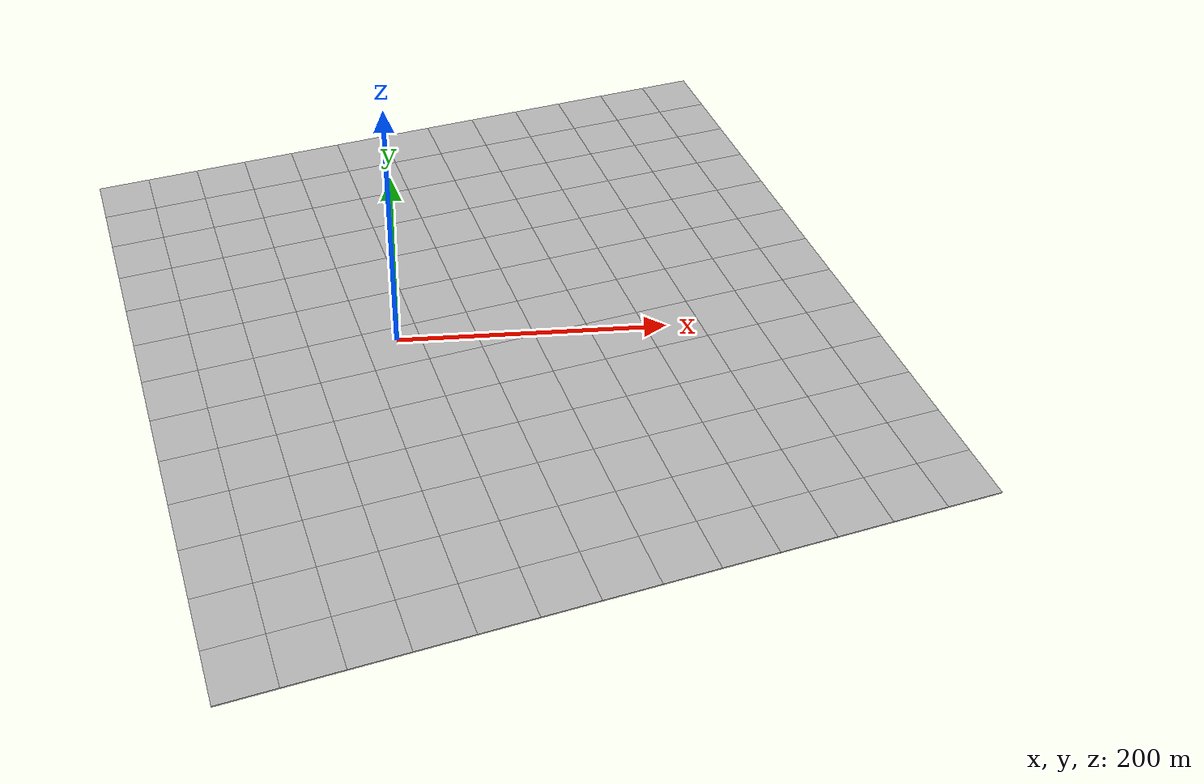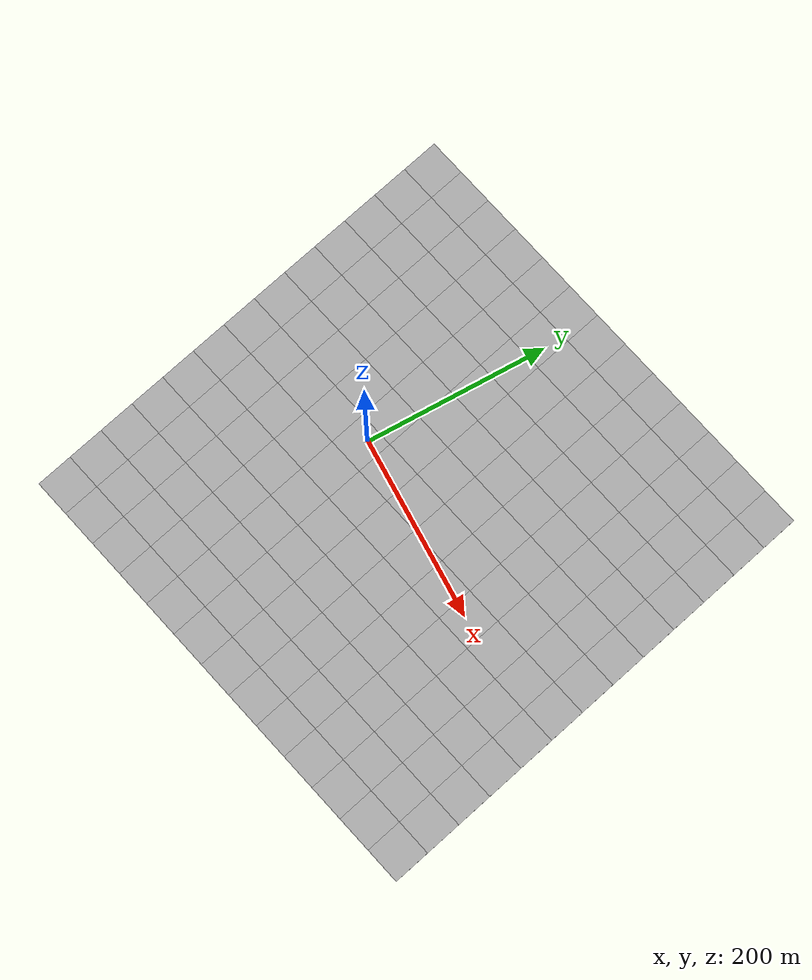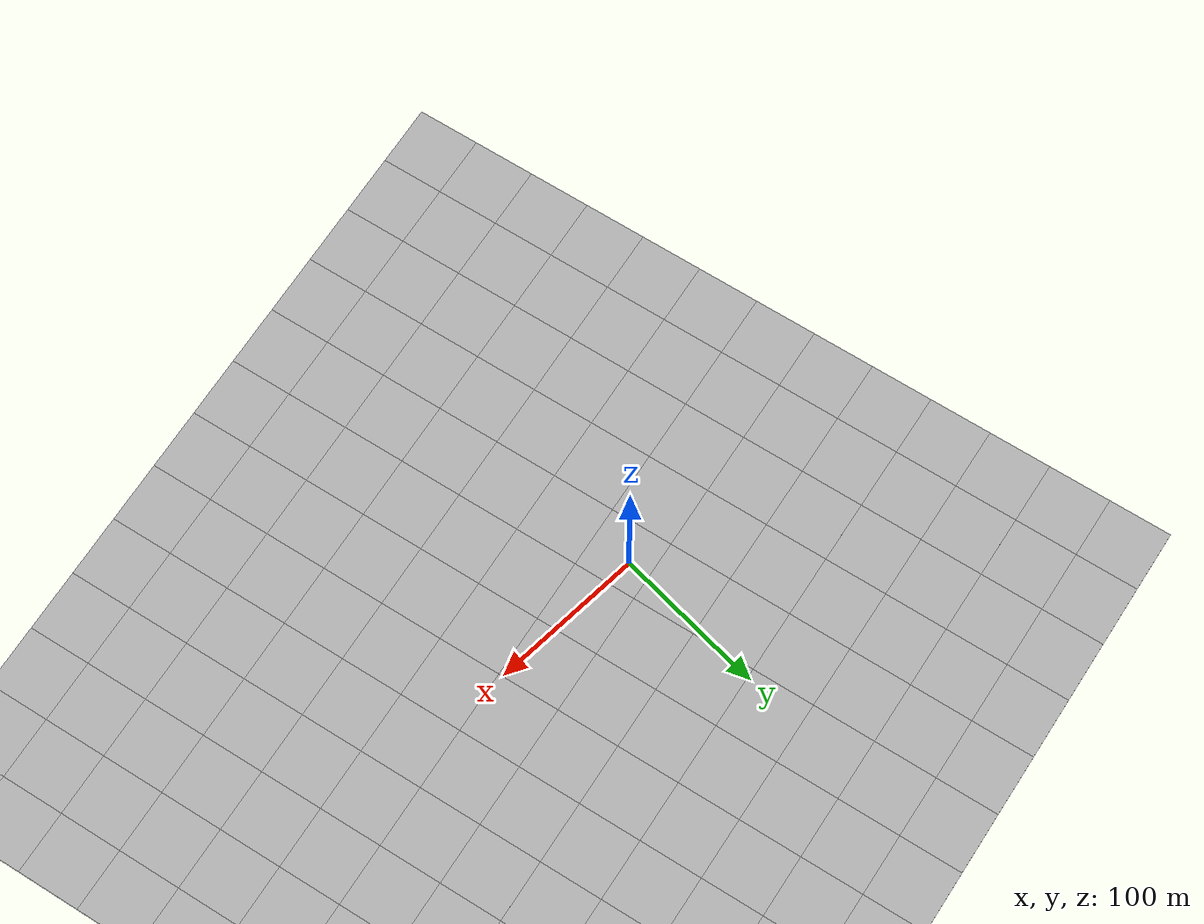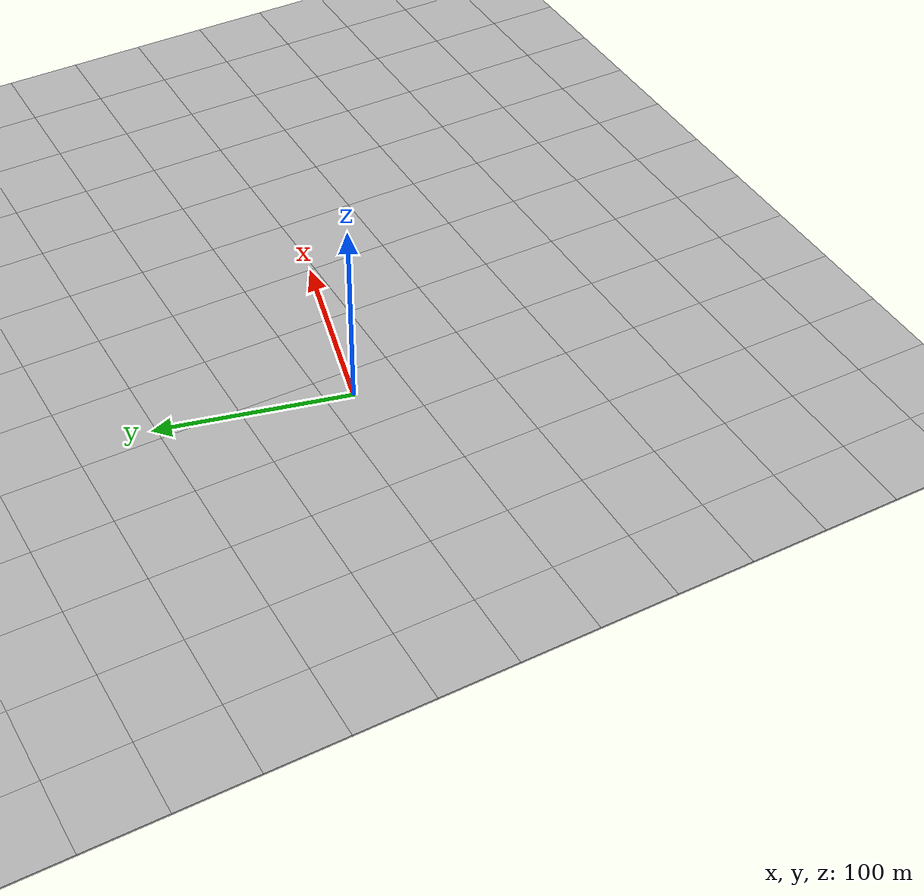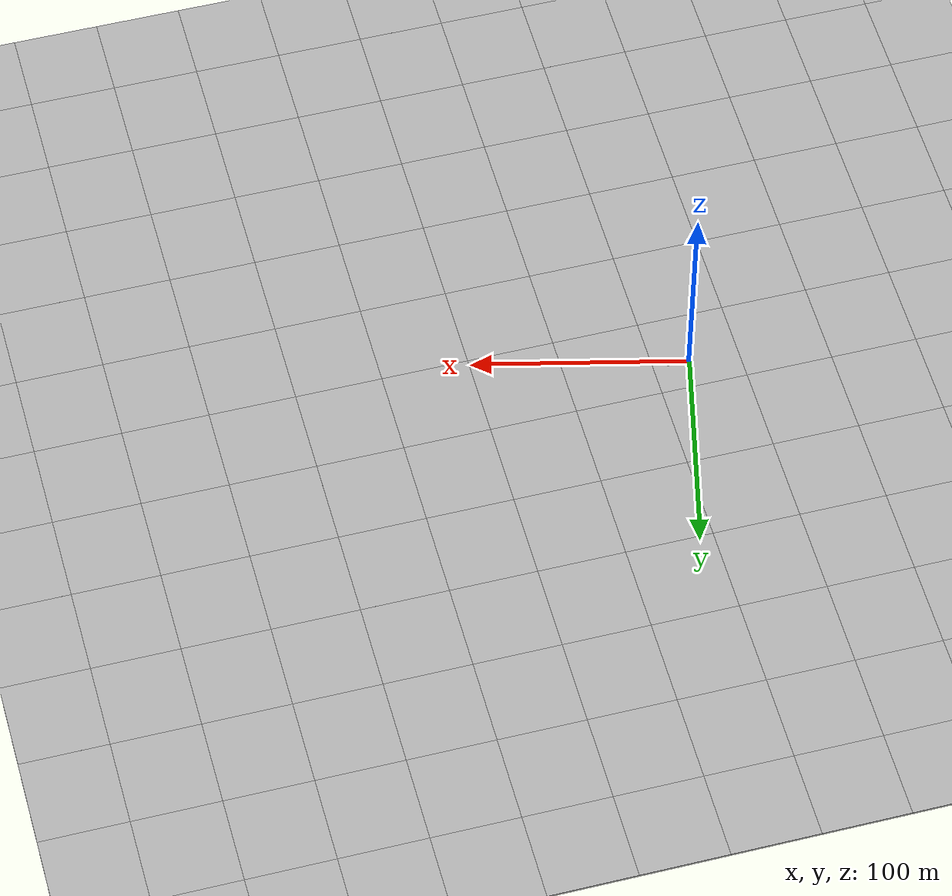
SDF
<sdf version="1.6">
 <world name="default">
  <light name="sun" type="directional">
   <pose>0 0 10 0 -0 0</pose>
   <diffuse>0.8 0.8 0.8 1</diffuse>
   <specular>0.2 0.2 0.2 1</specular>
   <attenuation>
    <range>1000</range>
    <constant>0.9</constant>
    <linear>0.01</linear>
    <quadratic>0.001</quadratic>
   </attenuation>
   <direction>-0.5 0.1 -0.9</direction>
  </light>
  <physics name="default_physics" default="0" type="ode">
   <ode>
    <solver>
     <type>quick</type>
     <iters>10</iters>
     <sor>1.3</sor>
     <use_dynamic_moi_rescaling>0</use_dynamic_moi_rescaling>
    </solver>
    <constraints>
     <cfm>0</cfm>
     <erp>0.2</erp>
     <contact_max_correcting_vel>100</contact_max_correcting_vel>
     <contact_surface_layer>0.001</contact_surface_layer>
    </constraints>
   </ode>
   <max_step_size>0.002</max_step_size>
   <real_time_factor>1</real_time_factor>
   <real_time_update_rate>500</real_time_update_rate>
  </physics>
  <scene><ambient>0.4 0.4 0.4 1</ambient><background>0.7 0.7 0.7 1</background><shadows>1</shadows></scene>
  <spherical_coordinates>
   <surface_model>EARTH_WGS84</surface_model>
   <latitude_deg>0</latitude_deg>
   <longitude_deg>0</longitude_deg>
   <elevation>0</elevation>
   <heading_deg>0</heading_deg>
  </spherical_coordinates>
  <plugin name="map" filename="libStaticMapPlugin.so">
   <center>32.2660215 -111.2735455</center>
   <world_size>500</world_size>
   <pose>76.900558 12.304379 0 0 0 -1.331975</pose>
   <map_type>satellite</map_type>
   <api_key>YOUR GOOGLE API KEY</api_key>
   <use_cache>true</use_cache>
  </plugin>
  <gravity>0 0 -9.8</gravity>
  <magnetic_field>6e-06 2.3e-05 -4.2e-05</magnetic_field>
  <atmosphere type="adiabatic"/>
  <model name="map_satellite_32.2660215_-111.273545_500_500">
   <static>1</static>
   <link name="link">
    <collision name="collision">
     <pose>0 0 -0.5 0 -0 0</pose>
     <geometry><box><size>525.147 525.147 1</size></box></geometry>
    </collision>
    <visual name="visual0_0">
     <pose>-242.376 242.376 -0.5 0 -0 1.5708</pose>
     <geometry><box><size>40.3959 40.3959 1</size></box></geometry>
     <material>
      <script>
       <uri>model://map_satellite_32.2660215_-111.273545_500_500/materials/scripts</uri>
       <uri>model://map_satellite_32.2660215_-111.273545_500_500/materials/textures</uri>
       <name>map_satellite_32.2660215_-111.273545_500_500/0_0</name>
      </script>
     </material>
    </visual>
    <visual name="visual0_1">
     <pose>-201.98 242.376 -0.5 0 -0 1.5708</pose>
     <geometry><box><size>40.3959 40.3959 1</size></box></geometry>
     <material>
      <script>
       <uri>model://map_satellite_32.2660215_-111.273545_500_500/materials/scripts</uri>
       <uri>model://map_satellite_32.2660215_-111.273545_500_500/materials/textures</uri>
       <name>map_satellite_32.2660215_-111.273545_500_500/0_1</name>
      </script>
     </material>
    </visual>
    <visual name="visual0_2">
     <pose>-161.584 242.376 -0.5 0 -0 1.5708</pose>
     <geometry><box><size>40.3959 40.3959 1</size></box></geometry>
     <material>
      <script>
       <uri>model://map_satellite_32.2660215_-111.273545_500_500/materials/scripts</uri>
       <uri>model://map_satellite_32.2660215_-111.273545_500_500/materials/textures</uri>
       <name>map_satellite_32.2660215_-111.273545_500_500/0_2</name>
      </script>
     </material>
    </visual>
    <visual name="visual0_3">
     <pose>-121.188 242.376 -0.5 0 -0 1.5708</pose>
     <geometry><box><size>40.3959 40.3959 1</size></box></geometry>
     <material>
      <script>
       <uri>model://map_satellite_32.2660215_-111.273545_500_500/materials/scripts</uri>
       <uri>model://map_satellite_32.2660215_-111.273545_500_500/materials/textures</uri>
       <name>map_satellite_32.2660215_-111.273545_500_500/0_3</name>
      </script>
     </material>
    </visual>
    <visual name="visual0_4">
     <pose>-80.7919 242.376 -0.5 0 -0 1.5708</pose>
     <geometry><box><size>40.3959 40.3959 1</size></box></geometry>
     <material>
      <script>
       <uri>model://map_satellite_32.2660215_-111.273545_500_500/materials/scripts</uri>
       <uri>model://map_satellite_32.2660215_-111.273545_500_500/materials/textures</uri>
       <name>map_satellite_32.2660215_-111.273545_500_500/0_4</name>
      </script>
     </material>
    </visual>
    <visual name="visual0_5">
     <pose>-40.3959 242.376 -0.5 0 -0 1.5708</pose>
     <geometry><box><size>40.3959 40.3959 1</size></box></geometry>
     <material>
      <script>
       <uri>model://map_satellite_32.2660215_-111.273545_500_500/materials/scripts</uri>
       <uri>model://map_satellite_32.2660215_-111.273545_500_500/materials/textures</uri>
       <name>map_satellite_32.2660215_-111.273545_500_500/0_5</name>
      </script>
     </material>
    </visual>
    <visual name="visual0_6">
     <pose>-0 242.376 -0.5 0 -0 1.5708</pose>
     <geometry><box><size>40.3959 40.3959 1</size></box></geometry>
     <material>
      <script>
       <uri>model://map_satellite_32.2660215_-111.273545_500_500/materials/scripts</uri>
       <uri>model://map_satellite_32.2660215_-111.273545_500_500/materials/textures</uri>
       <name>map_satellite_32.2660215_-111.273545_500_500/0_6</name>
      </script>
     </material>
    </visual>
    <visual name="visual0_7">
     <pose>40.3959 242.376 -0.5 0 -0 1.5708</pose>
     <geometry><box><size>40.3959 40.3959 1</size></box></geometry>
     <material>
      <script>
       <uri>model://map_satellite_32.2660215_-111.273545_500_500/materials/scripts</uri>
       <uri>model://map_satellite_32.2660215_-111.273545_500_500/materials/textures</uri>
       <name>map_satellite_32.2660215_-111.273545_500_500/0_7</name>
      </script>
     </material>
    </visual>
    <visual name="visual0_8">
     <pose>80.7919 242.376 -0.5 0 -0 1.5708</pose>
     <geometry><box><size>40.3959 40.3959 1</size></box></geometry>
     <material>
      <script>
       <uri>model://map_satellite_32.2660215_-111.273545_500_500/materials/scripts</uri>
       <uri>model://map_satellite_32.2660215_-111.273545_500_500/materials/textures</uri>
       <name>map_satellite_32.2660215_-111.273545_500_500/0_8</name>
      </script>
     </material>
    </visual>
    <visual name="visual0_9">
     <pose>121.188 242.376 -0.5 0 -0 1.5708</pose>
     <geometry><box><size>40.3959 40.3959 1</size></box></geometry>
     <material>
      <script>
       <uri>model://map_satellite_32.2660215_-111.273545_500_500/materials/scripts</uri>
       <uri>model://map_satellite_32.2660215_-111.273545_500_500/materials/textures</uri>
       <name>map_satellite_32.2660215_-111.273545_500_500/0_9</name>
      </script>
     </material>
    </visual>
    <visual name="visual0_10">
     <pose>161.584 242.376 -0.5 0 -0 1.5708</pose>
     <geometry><box><size>40.3959 40.3959 1</size></box></geometry>
     <material>
      <script>
       <uri>model://map_satellite_32.2660215_-111.273545_500_500/materials/scripts</uri>
       <uri>model://map_satellite_32.2660215_-111.273545_500_500/materials/textures</uri>
       <name>map_satellite_32.2660215_-111.273545_500_500/0_10</name>
      </script>
     </material>
    </visual>
    <visual name="visual0_11">
     <pose>201.98 242.376 -0.5 0 -0 1.5708</pose>
     <geometry><box><size>40.3959 40.3959 1</size></box></geometry>
     <material>
      <script>
       <uri>model://map_satellite_32.2660215_-111.273545_500_500/materials/scripts</uri>
       <uri>model://map_satellite_32.2660215_-111.273545_500_500/materials/textures</uri>
       <name>map_satellite_32.2660215_-111.273545_500_500/0_11</name>
      </script>
     </material>
    </visual>
    <visual name="visual0_12">
     <pose>242.376 242.376 -0.5 0 -0 1.5708</pose>
     <geometry><box><size>40.3959 40.3959 1</size></box></geometry>
     <material>
      <script>
       <uri>model://map_satellite_32.2660215_-111.273545_500_500/materials/scripts</uri>
       <uri>model://map_satellite_32.2660215_-111.273545_500_500/materials/textures</uri>
       <name>map_satellite_32.2660215_-111.273545_500_500/0_12</name>
      </script>
     </material>
    </visual>
    <visual name="visual1_0">
     <pose>-242.376 201.98 -0.5 0 -0 1.5708</pose>
     <geometry><box><size>40.3959 40.3959 1</size></box></geometry>
     <material>
      <script>
       <uri>model://map_satellite_32.2660215_-111.273545_500_500/materials/scripts</uri>
       <uri>model://map_satellite_32.2660215_-111.273545_500_500/materials/textures</uri>
       <name>map_satellite_32.2660215_-111.273545_500_500/1_0</name>
      </script>
     </material>
    </visual>
    <visual name="visual1_1">
     <pose>-201.98 201.98 -0.5 0 -0 1.5708</pose>
     <geometry><box><size>40.3959 40.3959 1</size></box></geometry>
     <material>
      <script>
       <uri>model://map_satellite_32.2660215_-111.273545_500_500/materials/scripts</uri>
       <uri>model://map_satellite_32.2660215_-111.273545_500_500/materials/textures</uri>
       <name>map_satellite_32.2660215_-111.273545_500_500/1_1</name>
      </script>
     </material>
    </visual>
    <visual name="visual1_2">
     <pose>-161.584 201.98 -0.5 0 -0 1.5708</pose>
     <geometry><box><size>40.3959 40.3959 1</size></box></geometry>
     <material>
      <script>
       <uri>model://map_satellite_32.2660215_-111.273545_500_500/materials/scripts</uri>
       <uri>model://map_satellite_32.2660215_-111.273545_500_500/materials/textures</uri>
       <name>map_satellite_32.2660215_-111.273545_500_500/1_2</name>
      </script>
     </material>
    </visual>
    <visual name="visual1_3">
     <pose>-121.188 201.98 -0.5 0 -0 1.5708</pose>
     <geometry><box><size>40.3959 40.3959 1</size></box></geometry>
     <material>
      <script>
       <uri>model://map_satellite_32.2660215_-111.273545_500_500/materials/scripts</uri>
       <uri>model://map_satellite_32.2660215_-111.273545_500_500/materials/textures</uri>
       <name>map_satellite_32.2660215_-111.273545_500_500/1_3</name>
      </script>
     </material>
    </visual>
    <visual name="visual1_4">
     <pose>-80.7919 201.98 -0.5 0 -0 1.5708</pose>
     <geometry><box><size>40.3959 40.3959 1</size></box></geometry>
     <material>
      <script>
       <uri>model://map_satellite_32.2660215_-111.273545_500_500/materials/scripts</uri>
       <uri>model://map_satellite_32.2660215_-111.273545_500_500/materials/textures</uri>
       <name>map_satellite_32.2660215_-111.273545_500_500/1_4</name>
      </script>
     </material>
    </visual>
    <visual name="visual1_5">
     <pose>-40.3959 201.98 -0.5 0 -0 1.5708</pose>
     <geometry><box><size>40.3959 40.3959 1</size></box></geometry>
     <material>
      <script>
       <uri>model://map_satellite_32.2660215_-111.273545_500_500/materials/scripts</uri>
       <uri>model://map_satellite_32.2660215_-111.273545_500_500/materials/textures</uri>
       <name>map_satellite_32.2660215_-111.273545_500_500/1_5</name>
      </script>
     </material>
    </visual>
    <visual name="visual1_6">
     <pose>-0 201.98 -0.5 0 -0 1.5708</pose>
     <geometry><box><size>40.3959 40.3959 1</size></box></geometry>
     <material>
      <script>
       <uri>model://map_satellite_32.2660215_-111.273545_500_500/materials/scripts</uri>
       <uri>model://map_satellite_32.2660215_-111.273545_500_500/materials/textures</uri>
       <name>map_satellite_32.2660215_-111.273545_500_500/1_6</name>
      </script>
     </material>
    </visual>
    <visual name="visual1_7">
     <pose>40.3959 201.98 -0.5 0 -0 1.5708</pose>
     <geometry><box><size>40.3959 40.3959 1</size></box></geometry>
     <material>
      <script>
       <uri>model://map_satellite_32.2660215_-111.273545_500_500/materials/scripts</uri>
       <uri>model://map_satellite_32.2660215_-111.273545_500_500/materials/textures</uri>
       <name>map_satellite_32.2660215_-111.273545_500_500/1_7</name>
      </script>
     </material>
    </visual>
    <visual name="visual1_8">
     <pose>80.7919 201.98 -0.5 0 -0 1.5708</pose>
     <geometry><box><size>40.3959 40.3959 1</size></box></geometry>
     <material>
      <script>
       <uri>model://map_satellite_32.2660215_-111.273545_500_500/materials/scripts</uri>
       <uri>model://map_satellite_32.2660215_-111.273545_500_500/materials/textures</uri>
       <name>map_satellite_32.2660215_-111.273545_500_500/1_8</name>
      </script>
     </material>
    </visual>
    <visual name="visual1_9">
     <pose>121.188 201.98 -0.5 0 -0 1.5708</pose>
     <geometry><box><size>40.3959 40.3959 1</size></box></geometry>
     <material>
      <script>
       <uri>model://map_satellite_32.2660215_-111.273545_500_500/materials/scripts</uri>
       <uri>model://map_satellite_32.2660215_-111.273545_500_500/materials/textures</uri>
       <name>map_satellite_32.2660215_-111.273545_500_500/1_9</name>
      </script>
     </material>
    </visual>
    <visual name="visual1_10">
     <pose>161.584 201.98 -0.5 0 -0 1.5708</pose>
     <geometry><box><size>40.3959 40.3959 1</size></box></geometry>
     <material>
      <script>
       <uri>model://map_satellite_32.2660215_-111.273545_500_500/materials/scripts</uri>
       <uri>model://map_satellite_32.2660215_-111.273545_500_500/materials/textures</uri>
       <name>map_satellite_32.2660215_-111.273545_500_500/1_10</name>
      </script>
     </material>
    </visual>
    <visual name="visual1_11">
     <pose>201.98 201.98 -0.5 0 -0 1.5708</pose>
     <geometry><box><size>40.3959 40.3959 1</size></box></geometry>
     <material>
      <script>
       <uri>model://map_satellite_32.2660215_-111.273545_500_500/materials/scripts</uri>
       <uri>model://map_satellite_32.2660215_-111.273545_500_500/materials/textures</uri>
       <name>map_satellite_32.2660215_-111.273545_500_500/1_11</name>
      </script>
     </material>
    </visual>
    <visual name="visual1_12">
     <pose>242.376 201.98 -0.5 0 -0 1.5708</pose>
     <geometry><box><size>40.3959 40.3959 1</size></box></geometry>
     <material>
      <script>
       <uri>model://map_satellite_32.2660215_-111.273545_500_500/materials/scripts</uri>
       <uri>model://map_satellite_32.2660215_-111.273545_500_500/materials/textures</uri>
       <name>map_satellite_32.2660215_-111.273545_500_500/1_12</name>
      </script>
     </material>
    </visual>
    <visual name="visual2_0">
     <pose>-242.376 161.584 -0.5 0 -0 1.5708</pose>
     <geometry><box><size>40.3959 40.3959 1</size></box></geometry>
     <material>
      <script>
       <uri>model://map_satellite_32.2660215_-111.273545_500_500/materials/scripts</uri>
       <uri>model://map_satellite_32.2660215_-111.273545_500_500/materials/textures</uri>
       <name>map_satellite_32.2660215_-111.273545_500_500/2_0</name>
      </script>
     </material>
    </visual>
    <visual name="visual2_1">
     <pose>-201.98 161.584 -0.5 0 -0 1.5708</pose>
     <geometry><box><size>40.3959 40.3959 1</size></box></geometry>
     <material>
      <script>
       <uri>model://map_satellite_32.2660215_-111.273545_500_500/materials/scripts</uri>
       <uri>model://map_satellite_32.2660215_-111.273545_500_500/materials/textures</uri>
       <name>map_satellite_32.2660215_-111.273545_500_500/2_1</name>
      </script>
     </material>
    </visual>
    <visual name="visual2_2">
     <pose>-161.584 161.584 -0.5 0 -0 1.5708</pose>
     <geometry><box><size>40.3959 40.3959 1</size></box></geometry>
     <material>
      <script>
       <uri>model://map_satellite_32.2660215_-111.273545_500_500/materials/scripts</uri>
       <uri>model://map_satellite_32.2660215_-111.273545_500_500/materials/textures</uri>
       <name>map_satellite_32.2660215_-111.273545_500_500/2_2</name>
      </script>
     </material>
    </visual>
    <visual name="visual2_3">
     <pose>-121.188 161.584 -0.5 0 -0 1.5708</pose>
     <geometry><box><size>40.3959 40.3959 1</size></box></geometry>
     <material>
      <script>
       <uri>model://map_satellite_32.2660215_-111.273545_500_500/materials/scripts</uri>
       <uri>model://map_satellite_32.2660215_-111.273545_500_500/materials/textures</uri>
       <name>map_satellite_32.2660215_-111.273545_500_500/2_3</name>
      </script>
     </material>
    </visual>
    <visual name="visual2_4">
     <pose>-80.7919 161.584 -0.5 0 -0 1.5708</pose>
     <geometry><box><size>40.3959 40.3959 1</size></box></geometry>
     <material>
      <script>
       <uri>model://map_satellite_32.2660215_-111.273545_500_500/materials/scripts</uri>
       <uri>model://map_satellite_32.2660215_-111.273545_500_500/materials/textures</uri>
       <name>map_satellite_32.2660215_-111.273545_500_500/2_4</name>
      </script>
     </material>
    </visual>
    <visual name="visual2_5">
     <pose>-40.3959 161.584 -0.5 0 -0 1.5708</pose>
     <geometry><box><size>40.3959 40.3959 1</size></box></geometry>
     <material>
      <script>
       <uri>model://map_satellite_32.2660215_-111.273545_500_500/materials/scripts</uri>
       <uri>model://map_satellite_32.2660215_-111.273545_500_500/materials/textures</uri>
       <name>map_satellite_32.2660215_-111.273545_500_500/2_5</name>
      </script>
     </material>
    </visual>
    <visual name="visual2_6">
     <pose>-0 161.584 -0.5 0 -0 1.5708</pose>
     <geometry><box><size>40.3959 40.3959 1</size></box></geometry>
     <material>
      <script>
       <uri>model://map_satellite_32.2660215_-111.273545_500_500/materials/scripts</uri>
       <uri>model://map_satellite_32.2660215_-111.273545_500_500/materials/textures</uri>
       <name>map_satellite_32.2660215_-111.273545_500_500/2_6</name>
      </script>
     </material>
    </visual>
    <visual name="visual2_7">
     <pose>40.3959 161.584 -0.5 0 -0 1.5708</pose>
     <geometry><box><size>40.3959 40.3959 1</size></box></geometry>
     <material>
      <script>
       <uri>model://map_satellite_32.2660215_-111.273545_500_500/materials/scripts</uri>
       <uri>model://map_satellite_32.2660215_-111.273545_500_500/materials/textures</uri>
       <name>map_satellite_32.2660215_-111.273545_500_500/2_7</name>
      </script>
     </material>
    </visual>
    <visual name="visual2_8">
     <pose>80.7919 161.584 -0.5 0 -0 1.5708</pose>
     <geometry><box><size>40.3959 40.3959 1</size></box></geometry>
     <material>
      <script>
       <uri>model://map_satellite_32.2660215_-111.273545_500_500/materials/scripts</uri>
       <uri>model://map_satellite_32.2660215_-111.273545_500_500/materials/textures</uri>
       <name>map_satellite_32.2660215_-111.273545_500_500/2_8</name>
      </script>
     </material>
    </visual>
    <visual name="visual2_9">
     <pose>121.188 161.584 -0.5 0 -0 1.5708</pose>
     <geometry><box><size>40.3959 40.3959 1</size></box></geometry>
     <material>
      <script>
       <uri>model://map_satellite_32.2660215_-111.273545_500_500/materials/scripts</uri>
       <uri>model://map_satellite_32.2660215_-111.273545_500_500/materials/textures</uri>
       <name>map_satellite_32.2660215_-111.273545_500_500/2_9</name>
      </script>
     </material>
    </visual>
    <visual name="visual2_10">
     <pose>161.584 161.584 -0.5 0 -0 1.5708</pose>
     <geometry><box><size>40.3959 40.3959 1</size></box></geometry>
     <material>
      <script>
       <uri>model://map_satellite_32.2660215_-111.273545_500_500/materials/scripts</uri>
       <uri>model://map_satellite_32.2660215_-111.273545_500_500/materials/textures</uri>
       <name>map_satellite_32.2660215_-111.273545_500_500/2_10</name>
      </script>
     </material>
    </visual>
    <visual name="visual2_11">
     <pose>201.98 161.584 -0.5 0 -0 1.5708</pose>
     <geometry><box><size>40.3959 40.3959 1</size></box></geometry>
     <material>
      <script>
       <uri>model://map_satellite_32.2660215_-111.273545_500_500/materials/scripts</uri>
       <uri>model://map_satellite_32.2660215_-111.273545_500_500/materials/textures</uri>
       <name>map_satellite_32.2660215_-111.273545_500_500/2_11</name>
      </script>
     </material>
    </visual>
    <visual name="visual2_12">
     <pose>242.376 161.584 -0.5 0 -0 1.5708</pose>
     <geometry><box><size>40.3959 40.3959 1</size></box></geometry>
     <material>
      <script>
       <uri>model://map_satellite_32.2660215_-111.273545_500_500/materials/scripts</uri>
       <uri>model://map_satellite_32.2660215_-111.273545_500_500/materials/textures</uri>
       <name>map_satellite_32.2660215_-111.273545_500_500/2_12</name>
      </script>
     </material>
    </visual>
    <visual name="visual3_0">
     <pose>-242.376 121.188 -0.5 0 -0 1.5708</pose>
     <geometry><box><size>40.3959 40.3959 1</size></box></geometry>
     <material>
      <script>
       <uri>model://map_satellite_32.2660215_-111.273545_500_500/materials/scripts</uri>
       <uri>model://map_satellite_32.2660215_-111.273545_500_500/materials/textures</uri>
       <name>map_satellite_32.2660215_-111.273545_500_500/3_0</name>
      </script>
     </material>
    </visual>
    <visual name="visual3_1">
     <pose>-201.98 121.188 -0.5 0 -0 1.5708</pose>
     <geometry><box><size>40.3959 40.3959 1</size></box></geometry>
     <material>
      <script>
       <uri>model://map_satellite_32.2660215_-111.273545_500_500/materials/scripts</uri>
       <uri>model://map_satellite_32.2660215_-111.273545_500_500/materials/textures</uri>
       <name>map_satellite_32.2660215_-111.273545_500_500/3_1</name>
      </script>
     </material>
    </visual>
    <visual name="visual3_2">
     <pose>-161.584 121.188 -0.5 0 -0 1.5708</pose>
     <geometry><box><size>40.3959 40.3959 1</size></box></geometry>
     <material>
      <script>
       <uri>model://map_satellite_32.2660215_-111.273545_500_500/materials/scripts</uri>
       <uri>model://map_satellite_32.2660215_-111.273545_500_500/materials/textures</uri>
       <name>map_satellite_32.2660215_-111.273545_500_500/3_2</name>
      </script>
     </material>
    </visual>
    <visual name="visual3_3">
     <pose>-121.188 121.188 -0.5 0 -0 1.5708</pose>
     <geometry><box><size>40.3959 40.3959 1</size></box></geometry>
     <material>
      <script>
       <uri>model://map_satellite_32.2660215_-111.273545_500_500/materials/scripts</uri>
       <uri>model://map_satellite_32.2660215_-111.273545_500_500/materials/textures</uri>
       <name>map_satellite_32.2660215_-111.273545_500_500/3_3</name>
      </script>
     </material>
    </visual>
    <visual name="visual3_4">
     <pose>-80.7919 121.188 -0.5 0 -0 1.5708</pose>
     <geometry><box><size>40.3959 40.3959 1</size></box></geometry>
     <material>
      <script>
       <uri>model://map_satellite_32.2660215_-111.273545_500_500/materials/scripts</uri>
       <uri>model://map_satellite_32.2660215_-111.273545_500_500/materials/textures</uri>
       <name>map_satellite_32.2660215_-111.273545_500_500/3_4</name>
      </script>
     </material>
    </visual>
    <visual name="visual3_5">
     <pose>-40.3959 121.188 -0.5 0 -0 1.5708</pose>
     <geometry><box><size>40.3959 40.3959 1</size></box></geometry>
     <material>
      <script>
       <uri>model://map_satellite_32.2660215_-111.273545_500_500/materials/scripts</uri>
       <uri>model://map_satellite_32.2660215_-111.273545_500_500/materials/textures</uri>
       <name>map_satellite_32.2660215_-111.273545_500_500/3_5</name>
      </script>
     </material>
    </visual>
    <visual name="visual3_6">
     <pose>-0 121.188 -0.5 0 -0 1.5708</pose>
     <geometry><box><size>40.3959 40.3959 1</size></box></geometry>
     <material>
      <script>
       <uri>model://map_satellite_32.2660215_-111.273545_500_500/materials/scripts</uri>
       <uri>model://map_satellite_32.2660215_-111.273545_500_500/materials/textures</uri>
       <name>map_satellite_32.2660215_-111.273545_500_500/3_6</name>
      </script>
     </material>
    </visual>
    <visual name="visual3_7">
     <pose>40.3959 121.188 -0.5 0 -0 1.5708</pose>
     <geometry><box><size>40.3959 40.3959 1</size></box></geometry>
     <material>
      <script>
       <uri>model://map_satellite_32.2660215_-111.273545_500_500/materials/scripts</uri>
       <uri>model://map_satellite_32.2660215_-111.273545_500_500/materials/textures</uri>
       <name>map_satellite_32.2660215_-111.273545_500_500/3_7</name>
      </script>
     </material>
    </visual>
    <visual name="visual3_8">
     <pose>80.7919 121.188 -0.5 0 -0 1.5708</pose>
     <geometry><box><size>40.3959 40.3959 1</size></box></geometry>
     <material>
      <script>
       <uri>model://map_satellite_32.2660215_-111.273545_500_500/materials/scripts</uri>
       <uri>model://map_satellite_32.2660215_-111.273545_500_500/materials/textures</uri>
       <name>map_satellite_32.2660215_-111.273545_500_500/3_8</name>
      </script>
     </material>
    </visual>
    <visual name="visual3_9">
     <pose>121.188 121.188 -0.5 0 -0 1.5708</pose>
     <geometry><box><size>40.3959 40.3959 1</size></box></geometry>
     <material>
      <script>
       <uri>model://map_satellite_32.2660215_-111.273545_500_500/materials/scripts</uri>
       <uri>model://map_satellite_32.2660215_-111.273545_500_500/materials/textures</uri>
       <name>map_satellite_32.2660215_-111.273545_500_500/3_9</name>
      </script>
     </material>
    </visual>
    <visual name="visual3_10">
     <pose>161.584 121.188 -0.5 0 -0 1.5708</pose>
     <geometry><box><size>40.3959 40.3959 1</size></box></geometry>
     <material>
      <script>
       <uri>model://map_satellite_32.2660215_-111.273545_500_500/materials/scripts</uri>
       <uri>model://map_satellite_32.2660215_-111.273545_500_500/materials/textures</uri>
       <name>map_satellite_32.2660215_-111.273545_500_500/3_10</name>
      </script>
     </material>
    </visual>
    <visual name="visual3_11">
     <pose>201.98 121.188 -0.5 0 -0 1.5708</pose>
     <geometry><box><size>40.3959 40.3959 1</size></box></geometry>
     <material>
      <script>
       <uri>model://map_satellite_32.2660215_-111.273545_500_500/materials/scripts</uri>
       <uri>model://map_satellite_32.2660215_-111.273545_500_500/materials/textures</uri>
       <name>map_satellite_32.2660215_-111.273545_500_500/3_11</name>
      </script>
     </material>
    </visual>
    <visual name="visual3_12">
     <pose>242.376 121.188 -0.5 0 -0 1.5708</pose>
     <geometry><box><size>40.3959 40.3959 1</size></box></geometry>
     <material>
      <script>
       <uri>model://map_satellite_32.2660215_-111.273545_500_500/materials/scripts</uri>
       <uri>model://map_satellite_32.2660215_-111.273545_500_500/materials/textures</uri>
       <name>map_satellite_32.2660215_-111.273545_500_500/3_12</name>
      </script>
     </material>
    </visual>
    <visual name="visual4_0">
     <pose>-242.376 80.7919 -0.5 0 -0 1.5708</pose>
     <geometry><box><size>40.3959 40.3959 1</size></box></geometry>
     <material>
      <script>
       <uri>model://map_satellite_32.2660215_-111.273545_500_500/materials/scripts</uri>
       <uri>model://map_satellite_32.2660215_-111.273545_500_500/materials/textures</uri>
       <name>map_satellite_32.2660215_-111.273545_500_500/4_0</name>
      </script>
     </material>
    </visual>
    <visual name="visual4_1">
     <pose>-201.98 80.7919 -0.5 0 -0 1.5708</pose>
     <geometry><box><size>40.3959 40.3959 1</size></box></geometry>
     <material>
      <script>
       <uri>model://map_satellite_32.2660215_-111.273545_500_500/materials/scripts</uri>
       <uri>model://map_satellite_32.2660215_-111.273545_500_500/materials/textures</uri>
       <name>map_satellite_32.2660215_-111.273545_500_500/4_1</name>
      </script>
     </material>
    </visual>
    <visual name="visual4_2">
     <pose>-161.584 80.7919 -0.5 0 -0 1.5708</pose>
     <geometry><box><size>40.3959 40.3959 1</size></box></geometry>
     <material>
      <script>
       <uri>model://map_satellite_32.2660215_-111.273545_500_500/materials/scripts</uri>
       <uri>model://map_satellite_32.2660215_-111.273545_500_500/materials/textures</uri>
       <name>map_satellite_32.2660215_-111.273545_500_500/4_2</name>
      </script>
     </material>
    </visual>
    <visual name="visual4_3">
     <pose>-121.188 80.7919 -0.5 0 -0 1.5708</pose>
     <geometry><box><size>40.3959 40.3959 1</size></box></geometry>
     <material>
      <script>
       <uri>model://map_satellite_32.2660215_-111.273545_500_500/materials/scripts</uri>
       <uri>model://map_satellite_32.2660215_-111.273545_500_500/materials/textures</uri>
       <name>map_satellite_32.2660215_-111.273545_500_500/4_3</name>
      </script>
     </material>
    </visual>
    <visual name="visual4_4">
     <pose>-80.7919 80.7919 -0.5 0 -0 1.5708</pose>
     <geometry><box><size>40.3959 40.3959 1</size></box></geometry>
     <material>
      <script>
       <uri>model://map_satellite_32.2660215_-111.273545_500_500/materials/scripts</uri>
       <uri>model://map_satellite_32.2660215_-111.273545_500_500/materials/textures</uri>
       <name>map_satellite_32.2660215_-111.273545_500_500/4_4</name>
      </script>
     </material>
    </visual>
    <visual name="visual4_5">
     <pose>-40.3959 80.7919 -0.5 0 -0 1.5708</pose>
     <geometry><box><size>40.3959 40.3959 1</size></box></geometry>
     <material>
      <script>
       <uri>model://map_satellite_32.2660215_-111.273545_500_500/materials/scripts</uri>
       <uri>model://map_satellite_32.2660215_-111.273545_500_500/materials/textures</uri>
       <name>map_satellite_32.2660215_-111.273545_500_500/4_5</name>
      </script>
     </material>
    </visual>
    <visual name="visual4_6">
     <pose>-0 80.7919 -0.5 0 -0 1.5708</pose>
     <geometry><box><size>40.3959 40.3959 1</size></box></geometry>
     <material>
      <script>
       <uri>model://map_satellite_32.2660215_-111.273545_500_500/materials/scripts</uri>
       <uri>model://map_satellite_32.2660215_-111.273545_500_500/materials/textures</uri>
       <name>map_satellite_32.2660215_-111.273545_500_500/4_6</name>
      </script>
     </material>
    </visual>
    <visual name="visual4_7">
     <pose>40.3959 80.7919 -0.5 0 -0 1.5708</pose>
     <geometry><box><size>40.3959 40.3959 1</size></box></geometry>
     <material>
      <script>
       <uri>model://map_satellite_32.2660215_-111.273545_500_500/materials/scripts</uri>
       <uri>model://map_satellite_32.2660215_-111.273545_500_500/materials/textures</uri>
       <name>map_satellite_32.2660215_-111.273545_500_500/4_7</name>
      </script>
     </material>
    </visual>
    <visual name="visual4_8">
     <pose>80.7919 80.7919 -0.5 0 -0 1.5708</pose>
     <geometry><box><size>40.3959 40.3959 1</size></box></geometry>
     <material>
      <script>
       <uri>model://map_satellite_32.2660215_-111.273545_500_500/materials/scripts</uri>
       <uri>model://map_satellite_32.2660215_-111.273545_500_500/materials/textures</uri>
       <name>map_satellite_32.2660215_-111.273545_500_500/4_8</name>
      </script>
     </material>
    </visual>
    <visual name="visual4_9">
     <pose>121.188 80.7919 -0.5 0 -0 1.5708</pose>
     <geometry><box><size>40.3959 40.3959 1</size></box></geometry>
     <material>
      <script>
       <uri>model://map_satellite_32.2660215_-111.273545_500_500/materials/scripts</uri>
       <uri>model://map_satellite_32.2660215_-111.273545_500_500/materials/textures</uri>
       <name>map_satellite_32.2660215_-111.273545_500_500/4_9</name>
      </script>
     </material>
    </visual>
    <visual name="visual4_10">
     <pose>161.584 80.7919 -0.5 0 -0 1.5708</pose>
     <geometry><box><size>40.3959 40.3959 1</size></box></geometry>
     <material>
      <script>
       <uri>model://map_satellite_32.2660215_-111.273545_500_500/materials/scripts</uri>
       <uri>model://map_satellite_32.2660215_-111.273545_500_500/materials/textures</uri>
       <name>map_satellite_32.2660215_-111.273545_500_500/4_10</name>
      </script>
     </material>
    </visual>
    <visual name="visual4_11">
     <pose>201.98 80.7919 -0.5 0 -0 1.5708</pose>
     <geometry><box><size>40.3959 40.3959 1</size></box></geometry>
     <material>
      <script>
       <uri>model://map_satellite_32.2660215_-111.273545_500_500/materials/scripts</uri>
       <uri>model://map_satellite_32.2660215_-111.273545_500_500/materials/textures</uri>
       <name>map_satellite_32.2660215_-111.273545_500_500/4_11</name>
      </script>
     </material>
    </visual>
    <visual name="visual4_12">
     <pose>242.376 80.7919 -0.5 0 -0 1.5708</pose>
     <geometry><box><size>40.3959 40.3959 1</size></box></geometry>
     <material>
      <script>
       <uri>model://map_satellite_32.2660215_-111.273545_500_500/materials/scripts</uri>
       <uri>model://map_satellite_32.2660215_-111.273545_500_500/materials/textures</uri>
       <name>map_satellite_32.2660215_-111.273545_500_500/4_12</name>
      </script>
     </material>
    </visual>
    <visual name="visual5_0">
     <pose>-242.376 40.3959 -0.5 0 -0 1.5708</pose>
     <geometry><box><size>40.3959 40.3959 1</size></box></geometry>
     <material>
      <script>
       <uri>model://map_satellite_32.2660215_-111.273545_500_500/materials/scripts</uri>
       <uri>model://map_satellite_32.2660215_-111.273545_500_500/materials/textures</uri>
       <name>map_satellite_32.2660215_-111.273545_500_500/5_0</name>
      </script>
     </material>
    </visual>
    <visual name="visual5_1">
     <pose>-201.98 40.3959 -0.5 0 -0 1.5708</pose>
     <geometry><box><size>40.3959 40.3959 1</size></box></geometry>
     <material>
      <script>
       <uri>model://map_satellite_32.2660215_-111.273545_500_500/materials/scripts</uri>
       <uri>model://map_satellite_32.2660215_-111.273545_500_500/materials/textures</uri>
       <name>map_satellite_32.2660215_-111.273545_500_500/5_1</name>
      </script>
     </material>
    </visual>
    <visual name="visual5_2">
     <pose>-161.584 40.3959 -0.5 0 -0 1.5708</pose>
     <geometry><box><size>40.3959 40.3959 1</size></box></geometry>
     <material>
      <script>
       <uri>model://map_satellite_32.2660215_-111.273545_500_500/materials/scripts</uri>
       <uri>model://map_satellite_32.2660215_-111.273545_500_500/materials/textures</uri>
       <name>map_satellite_32.2660215_-111.273545_500_500/5_2</name>
      </script>
     </material>
    </visual>
    <visual name="visual5_3">
     <pose>-121.188 40.3959 -0.5 0 -0 1.5708</pose>
     <geometry><box><size>40.3959 40.3959 1</size></box></geometry>
     <material>
      <script>
       <uri>model://map_satellite_32.2660215_-111.273545_500_500/materials/scripts</uri>
       <uri>model://map_satellite_32.2660215_-111.273545_500_500/materials/textures</uri>
       <name>map_satellite_32.2660215_-111.273545_500_500/5_3</name>
      </script>
     </material>
    </visual>
    <visual name="visual5_4">
     <pose>-80.7919 40.3959 -0.5 0 -0 1.5708</pose>
     <geometry><box><size>40.3959 40.3959 1</size></box></geometry>
     <material>
      <script>
       <uri>model://map_satellite_32.2660215_-111.273545_500_500/materials/scripts</uri>
       <uri>model://map_satellite_32.2660215_-111.273545_500_500/materials/textures</uri>
       <name>map_satellite_32.2660215_-111.273545_500_500/5_4</name>
      </script>
     </material>
    </visual>
    <visual name="visual5_5">
     <pose>-40.3959 40.3959 -0.5 0 -0 1.5708</pose>
     <geometry><box><size>40.3959 40.3959 1</size></box></geometry>
     <material>
      <script>
       <uri>model://map_satellite_32.2660215_-111.273545_500_500/materials/scripts</uri>
       <uri>model://map_satellite_32.2660215_-111.273545_500_500/materials/textures</uri>
       <name>map_satellite_32.2660215_-111.273545_500_500/5_5</name>
      </script>
     </material>
    </visual>
    <visual name="visual5_6">
     <pose>-0 40.3959 -0.5 0 -0 1.5708</pose>
     <geometry><box><size>40.3959 40.3959 1</size></box></geometry>
     <material>
      <script>
       <uri>model://map_satellite_32.2660215_-111.273545_500_500/materials/scripts</uri>
       <uri>model://map_satellite_32.2660215_-111.273545_500_500/materials/textures</uri>
       <name>map_satellite_32.2660215_-111.273545_500_500/5_6</name>
      </script>
     </material>
    </visual>
    <visual name="visual5_7">
     <pose>40.3959 40.3959 -0.5 0 -0 1.5708</pose>
     <geometry><box><size>40.3959 40.3959 1</size></box></geometry>
     <material>
      <script>
       <uri>model://map_satellite_32.2660215_-111.273545_500_500/materials/scripts</uri>
       <uri>model://map_satellite_32.2660215_-111.273545_500_500/materials/textures</uri>
       <name>map_satellite_32.2660215_-111.273545_500_500/5_7</name>
      </script>
     </material>
    </visual>
    <visual name="visual5_8">
     <pose>80.7919 40.3959 -0.5 0 -0 1.5708</pose>
     <geometry><box><size>40.3959 40.3959 1</size></box></geometry>
     <material>
      <script>
       <uri>model://map_satellite_32.2660215_-111.273545_500_500/materials/scripts</uri>
       <uri>model://map_satellite_32.2660215_-111.273545_500_500/materials/textures</uri>
       <name>map_satellite_32.2660215_-111.273545_500_500/5_8</name>
      </script>
     </material>
    </visual>
    <visual name="visual5_9">
     <pose>121.188 40.3959 -0.5 0 -0 1.5708</pose>
     <geometry><box><size>40.3959 40.3959 1</size></box></geometry>
     <material>
      <script>
       <uri>model://map_satellite_32.2660215_-111.273545_500_500/materials/scripts</uri>
       <uri>model://map_satellite_32.2660215_-111.273545_500_500/materials/textures</uri>
       <name>map_satellite_32.2660215_-111.273545_500_500/5_9</name>
      </script>
     </material>
    </visual>
    <visual name="visual5_10">
     <pose>161.584 40.3959 -0.5 0 -0 1.5708</pose>
     <geometry><box><size>40.3959 40.3959 1</size></box></geometry>
     <material>
      <script>
       <uri>model://map_satellite_32.2660215_-111.273545_500_500/materials/scripts</uri>
       <uri>model://map_satellite_32.2660215_-111.273545_500_500/materials/textures</uri>
       <name>map_satellite_32.2660215_-111.273545_500_500/5_10</name>
      </script>
     </material>
    </visual>
    <visual name="visual5_11">
     <pose>201.98 40.3959 -0.5 0 -0 1.5708</pose>
     <geometry><box><size>40.3959 40.3959 1</size></box></geometry>
     <material>
      <script>
       <uri>model://map_satellite_32.2660215_-111.273545_500_500/materials/scripts</uri>
       <uri>model://map_satellite_32.2660215_-111.273545_500_500/materials/textures</uri>
       <name>map_satellite_32.2660215_-111.273545_500_500/5_11</name>
      </script>
     </material>
    </visual>
    <visual name="visual5_12">
     <pose>242.376 40.3959 -0.5 0 -0 1.5708</pose>
     <geometry><box><size>40.3959 40.3959 1</size></box></geometry>
     <material>
      <script>
       <uri>model://map_satellite_32.2660215_-111.273545_500_500/materials/scripts</uri>
       <uri>model://map_satellite_32.2660215_-111.273545_500_500/materials/textures</uri>
       <name>map_satellite_32.2660215_-111.273545_500_500/5_12</name>
      </script>
     </material>
    </visual>
    <visual name="visual6_0">
     <pose>-242.376 0 -0.5 0 -0 1.5708</pose>
     <geometry><box><size>40.3959 40.3959 1</size></box></geometry>
     <material>
      <script>
       <uri>model://map_satellite_32.2660215_-111.273545_500_500/materials/scripts</uri>
       <uri>model://map_satellite_32.2660215_-111.273545_500_500/materials/textures</uri>
       <name>map_satellite_32.2660215_-111.273545_500_500/6_0</name>
      </script>
     </material>
    </visual>
    <visual name="visual6_1">
     <pose>-201.98 0 -0.5 0 -0 1.5708</pose>
     <geometry><box><size>40.3959 40.3959 1</size></box></geometry>
     <material>
      <script>
       <uri>model://map_satellite_32.2660215_-111.273545_500_500/materials/scripts</uri>
       <uri>model://map_satellite_32.2660215_-111.273545_500_500/materials/textures</uri>
       <name>map_satellite_32.2660215_-111.273545_500_500/6_1</name>
      </script>
     </material>
    </visual>
    <visual name="visual6_2">
     <pose>-161.584 0 -0.5 0 -0 1.5708</pose>
     <geometry><box><size>40.3959 40.3959 1</size></box></geometry>
     <material>
      <script>
       <uri>model://map_satellite_32.2660215_-111.273545_500_500/materials/scripts</uri>
       <uri>model://map_satellite_32.2660215_-111.273545_500_500/materials/textures</uri>
       <name>map_satellite_32.2660215_-111.273545_500_500/6_2</name>
      </script>
     </material>
    </visual>
    <visual name="visual6_3">
     <pose>-121.188 0 -0.5 0 -0 1.5708</pose>
     <geometry><box><size>40.3959 40.3959 1</size></box></geometry>
     <material>
      <script>
       <uri>model://map_satellite_32.2660215_-111.273545_500_500/materials/scripts</uri>
       <uri>model://map_satellite_32.2660215_-111.273545_500_500/materials/textures</uri>
       <name>map_satellite_32.2660215_-111.273545_500_500/6_3</name>
      </script>
     </material>
    </visual>
    <visual name="visual6_4">
     <pose>-80.7919 0 -0.5 0 -0 1.5708</pose>
     <geometry><box><size>40.3959 40.3959 1</size></box></geometry>
     <material>
      <script>
       <uri>model://map_satellite_32.2660215_-111.273545_500_500/materials/scripts</uri>
       <uri>model://map_satellite_32.2660215_-111.273545_500_500/materials/textures</uri>
       <name>map_satellite_32.2660215_-111.273545_500_500/6_4</name>
      </script>
     </material>
    </visual>
    <visual name="visual6_5">
     <pose>-40.3959 0 -0.5 0 -0 1.5708</pose>
     <geometry><box><size>40.3959 40.3959 1</size></box></geometry>
     <material>
      <script>
       <uri>model://map_satellite_32.2660215_-111.273545_500_500/materials/scripts</uri>
       <uri>model://map_satellite_32.2660215_-111.273545_500_500/materials/textures</uri>
       <name>map_satellite_32.2660215_-111.273545_500_500/6_5</name>
      </script>
     </material>
    </visual>
    <visual name="visual6_6">
     <pose>-0 0 -0.5 0 -0 1.5708</pose>
     <geometry><box><size>40.3959 40.3959 1</size></box></geometry>
     <material>
      <script>
       <uri>model://map_satellite_32.2660215_-111.273545_500_500/materials/scripts</uri>
       <uri>model://map_satellite_32.2660215_-111.273545_500_500/materials/textures</uri>
       <name>map_satellite_32.2660215_-111.273545_500_500/6_6</name>
      </script>
     </material>
    </visual>
    <visual name="visual6_7">
     <pose>40.3959 0 -0.5 0 -0 1.5708</pose>
     <geometry><box><size>40.3959 40.3959 1</size></box></geometry>
     <material>
      <script>
       <uri>model://map_satellite_32.2660215_-111.273545_500_500/materials/scripts</uri>
       <uri>model://map_satellite_32.2660215_-111.273545_500_500/materials/textures</uri>
       <name>map_satellite_32.2660215_-111.273545_500_500/6_7</name>
      </script>
     </material>
    </visual>
    <visual name="visual6_8">
     <pose>80.7919 0 -0.5 0 -0 1.5708</pose>
     <geometry><box><size>40.3959 40.3959 1</size></box></geometry>
     <material>
      <script>
       <uri>model://map_satellite_32.2660215_-111.273545_500_500/materials/scripts</uri>
       <uri>model://map_satellite_32.2660215_-111.273545_500_500/materials/textures</uri>
       <name>map_satellite_32.2660215_-111.273545_500_500/6_8</name>
      </script>
     </material>
    </visual>
    <visual name="visual6_9">
     <pose>121.188 0 -0.5 0 -0 1.5708</pose>
     <geometry><box><size>40.3959 40.3959 1</size></box></geometry>
     <material>
      <script>
       <uri>model://map_satellite_32.2660215_-111.273545_500_500/materials/scripts</uri>
       <uri>model://map_satellite_32.2660215_-111.273545_500_500/materials/textures</uri>
       <name>map_satellite_32.2660215_-111.273545_500_500/6_9</name>
      </script>
     </material>
    </visual>
    <visual name="visual6_10">
     <pose>161.584 0 -0.5 0 -0 1.5708</pose>
     <geometry><box><size>40.3959 40.3959 1</size></box></geometry>
     <material>
      <script>
       <uri>model://map_satellite_32.2660215_-111.273545_500_500/materials/scripts</uri>
       <uri>model://map_satellite_32.2660215_-111.273545_500_500/materials/textures</uri>
       <name>map_satellite_32.2660215_-111.273545_500_500/6_10</name>
      </script>
     </material>
    </visual>
    <visual name="visual6_11">
     <pose>201.98 0 -0.5 0 -0 1.5708</pose>
     <geometry><box><size>40.3959 40.3959 1</size></box></geometry>
     <material>
      <script>
       <uri>model://map_satellite_32.2660215_-111.273545_500_500/materials/scripts</uri>
       <uri>model://map_satellite_32.2660215_-111.273545_500_500/materials/textures</uri>
       <name>map_satellite_32.2660215_-111.273545_500_500/6_11</name>
      </script>
     </material>
    </visual>
    <visual name="visual6_12">
     <pose>242.376 0 -0.5 0 -0 1.5708</pose>
     <geometry><box><size>40.3959 40.3959 1</size></box></geometry>
     <material>
      <script>
       <uri>model://map_satellite_32.2660215_-111.273545_500_500/materials/scripts</uri>
       <uri>model://map_satellite_32.2660215_-111.273545_500_500/materials/textures</uri>
       <name>map_satellite_32.2660215_-111.273545_500_500/6_12</name>
      </script>
     </material>
    </visual>
    <visual name="visual7_0">
     <pose>-242.376 -40.3959 -0.5 0 -0 1.5708</pose>
     <geometry><box><size>40.3959 40.3959 1</size></box></geometry>
     <material>
      <script>
       <uri>model://map_satellite_32.2660215_-111.273545_500_500/materials/scripts</uri>
       <uri>model://map_satellite_32.2660215_-111.273545_500_500/materials/textures</uri>
       <name>map_satellite_32.2660215_-111.273545_500_500/7_0</name>
      </script>
     </material>
    </visual>
    <visual name="visual7_1">
     <pose>-201.98 -40.3959 -0.5 0 -0 1.5708</pose>
     <geometry><box><size>40.3959 40.3959 1</size></box></geometry>
     <material>
      <script>
       <uri>model://map_satellite_32.2660215_-111.273545_500_500/materials/scripts</uri>
       <uri>model://map_satellite_32.2660215_-111.273545_500_500/materials/textures</uri>
       <name>map_satellite_32.2660215_-111.273545_500_500/7_1</name>
      </script>
     </material>
    </visual>
    <visual name="visual7_2">
     <pose>-161.584 -40.3959 -0.5 0 -0 1.5708</pose>
     <geometry><box><size>40.3959 40.3959 1</size></box></geometry>
     <material>
      <script>
       <uri>model://map_satellite_32.2660215_-111.273545_500_500/materials/scripts</uri>
       <uri>model://map_satellite_32.2660215_-111.273545_500_500/materials/textures</uri>
       <name>map_satellite_32.2660215_-111.273545_500_500/7_2</name>
      </script>
     </material>
    </visual>
    <visual name="visual7_3">
     <pose>-121.188 -40.3959 -0.5 0 -0 1.5708</pose>
     <geometry><box><size>40.3959 40.3959 1</size></box></geometry>
     <material>
      <script>
       <uri>model://map_satellite_32.2660215_-111.273545_500_500/materials/scripts</uri>
       <uri>model://map_satellite_32.2660215_-111.273545_500_500/materials/textures</uri>
       <name>map_satellite_32.2660215_-111.273545_500_500/7_3</name>
      </script>
     </material>
    </visual>
    <visual name="visual7_4">
     <pose>-80.7919 -40.3959 -0.5 0 -0 1.5708</pose>
     <geometry><box><size>40.3959 40.3959 1</size></box></geometry>
     <material>
      <script>
       <uri>model://map_satellite_32.2660215_-111.273545_500_500/materials/scripts</uri>
       <uri>model://map_satellite_32.2660215_-111.273545_500_500/materials/textures</uri>
       <name>map_satellite_32.2660215_-111.273545_500_500/7_4</name>
      </script>
     </material>
    </visual>
    <visual name="visual7_5">
     <pose>-40.3959 -40.3959 -0.5 0 -0 1.5708</pose>
     <geometry><box><size>40.3959 40.3959 1</size></box></geometry>
     <material>
      <script>
       <uri>model://map_satellite_32.2660215_-111.273545_500_500/materials/scripts</uri>
       <uri>model://map_satellite_32.2660215_-111.273545_500_500/materials/textures</uri>
       <name>map_satellite_32.2660215_-111.273545_500_500/7_5</name>
      </script>
     </material>
    </visual>
    <visual name="visual7_6">
     <pose>-0 -40.3959 -0.5 0 -0 1.5708</pose>
     <geometry><box><size>40.3959 40.3959 1</size></box></geometry>
     <material>
      <script>
       <uri>model://map_satellite_32.2660215_-111.273545_500_500/materials/scripts</uri>
       <uri>model://map_satellite_32.2660215_-111.273545_500_500/materials/textures</uri>
       <name>map_satellite_32.2660215_-111.273545_500_500/7_6</name>
      </script>
     </material>
    </visual>
    <visual name="visual7_7">
     <pose>40.3959 -40.3959 -0.5 0 -0 1.5708</pose>
     <geometry><box><size>40.3959 40.3959 1</size></box></geometry>
     <material>
      <script>
       <uri>model://map_satellite_32.2660215_-111.273545_500_500/materials/scripts</uri>
       <uri>model://map_satellite_32.2660215_-111.273545_500_500/materials/textures</uri>
       <name>map_satellite_32.2660215_-111.273545_500_500/7_7</name>
      </script>
     </material>
    </visual>
    <visual name="visual7_8">
     <pose>80.7919 -40.3959 -0.5 0 -0 1.5708</pose>
     <geometry><box><size>40.3959 40.3959 1</size></box></geometry>
     <material>
      <script>
       <uri>model://map_satellite_32.2660215_-111.273545_500_500/materials/scripts</uri>
       <uri>model://map_satellite_32.2660215_-111.273545_500_500/materials/textures</uri>
       <name>map_satellite_32.2660215_-111.273545_500_500/7_8</name>
      </script>
     </material>
    </visual>
    <visual name="visual7_9">
     <pose>121.188 -40.3959 -0.5 0 -0 1.5708</pose>
     <geometry><box><size>40.3959 40.3959 1</size></box></geometry>
     <material>
      <script>
       <uri>model://map_satellite_32.2660215_-111.273545_500_500/materials/scripts</uri>
       <uri>model://map_satellite_32.2660215_-111.273545_500_500/materials/textures</uri>
       <name>map_satellite_32.2660215_-111.273545_500_500/7_9</name>
      </script>
     </material>
    </visual>
    <visual name="visual7_10">
     <pose>161.584 -40.3959 -0.5 0 -0 1.5708</pose>
     <geometry><box><size>40.3959 40.3959 1</size></box></geometry>
     <material>
      <script>
       <uri>model://map_satellite_32.2660215_-111.273545_500_500/materials/scripts</uri>
       <uri>model://map_satellite_32.2660215_-111.273545_500_500/materials/textures</uri>
       <name>map_satellite_32.2660215_-111.273545_500_500/7_10</name>
      </script>
     </material>
    </visual>
    <visual name="visual7_11">
     <pose>201.98 -40.3959 -0.5 0 -0 1.5708</pose>
     <geometry><box><size>40.3959 40.3959 1</size></box></geometry>
     <material>
      <script>
       <uri>model://map_satellite_32.2660215_-111.273545_500_500/materials/scripts</uri>
       <uri>model://map_satellite_32.2660215_-111.273545_500_500/materials/textures</uri>
       <name>map_satellite_32.2660215_-111.273545_500_500/7_11</name>
      </script>
     </material>
    </visual>
    <visual name="visual7_12">
     <pose>242.376 -40.3959 -0.5 0 -0 1.5708</pose>
     <geometry><box><size>40.3959 40.3959 1</size></box></geometry>
     <material>
      <script>
       <uri>model://map_satellite_32.2660215_-111.273545_500_500/materials/scripts</uri>
       <uri>model://map_satellite_32.2660215_-111.273545_500_500/materials/textures</uri>
       <name>map_satellite_32.2660215_-111.273545_500_500/7_12</name>
      </script>
     </material>
    </visual>
    <visual name="visual8_0">
     <pose>-242.376 -80.7919 -0.5 0 -0 1.5708</pose>
     <geometry><box><size>40.3959 40.3959 1</size></box></geometry>
     <material>
      <script>
       <uri>model://map_satellite_32.2660215_-111.273545_500_500/materials/scripts</uri>
       <uri>model://map_satellite_32.2660215_-111.273545_500_500/materials/textures</uri>
       <name>map_satellite_32.2660215_-111.273545_500_500/8_0</name>
      </script>
     </material>
    </visual>
    <visual name="visual8_1">
     <pose>-201.98 -80.7919 -0.5 0 -0 1.5708</pose>
     <geometry><box><size>40.3959 40.3959 1</size></box></geometry>
     <material>
      <script>
       <uri>model://map_satellite_32.2660215_-111.273545_500_500/materials/scripts</uri>
       <uri>model://map_satellite_32.2660215_-111.273545_500_500/materials/textures</uri>
       <name>map_satellite_32.2660215_-111.273545_500_500/8_1</name>
      </script>
     </material>
    </visual>
    <visual name="visual8_2">
     <pose>-161.584 -80.7919 -0.5 0 -0 1.5708</pose>
     <geometry><box><size>40.3959 40.3959 1</size></box></geometry>
     <material>
      <script>
       <uri>model://map_satellite_32.2660215_-111.273545_500_500/materials/scripts</uri>
       <uri>model://map_satellite_32.2660215_-111.273545_500_500/materials/textures</uri>
       <name>map_satellite_32.2660215_-111.273545_500_500/8_2</name>
      </script>
     </material>
    </visual>
    <visual name="visual8_3">
     <pose>-121.188 -80.7919 -0.5 0 -0 1.5708</pose>
     <geometry><box><size>40.3959 40.3959 1</size></box></geometry>
     <material>
      <script>
       <uri>model://map_satellite_32.2660215_-111.273545_500_500/materials/scripts</uri>
       <uri>model://map_satellite_32.2660215_-111.273545_500_500/materials/textures</uri>
       <name>map_satellite_32.2660215_-111.273545_500_500/8_3</name>
      </script>
     </material>
    </visual>
    <visual name="visual8_4">
     <pose>-80.7919 -80.7919 -0.5 0 -0 1.5708</pose>
     <geometry><box><size>40.3959 40.3959 1</size></box></geometry>
     <material>
      <script>
       <uri>model://map_satellite_32.2660215_-111.273545_500_500/materials/scripts</uri>
       <uri>model://map_satellite_32.2660215_-111.273545_500_500/materials/textures</uri>
       <name>map_satellite_32.2660215_-111.273545_500_500/8_4</name>
      </script>
     </material>
    </visual>
    <visual name="visual8_5">
     <pose>-40.3959 -80.7919 -0.5 0 -0 1.5708</pose>
     <geometry><box><size>40.3959 40.3959 1</size></box></geometry>
     <material>
      <script>
       <uri>model://map_satellite_32.2660215_-111.273545_500_500/materials/scripts</uri>
       <uri>model://map_satellite_32.2660215_-111.273545_500_500/materials/textures</uri>
       <name>map_satellite_32.2660215_-111.273545_500_500/8_5</name>
      </script>
     </material>
    </visual>
    <visual name="visual8_6">
     <pose>-0 -80.7919 -0.5 0 -0 1.5708</pose>
     <geometry><box><size>40.3959 40.3959 1</size></box></geometry>
     <material>
      <script>
       <uri>model://map_satellite_32.2660215_-111.273545_500_500/materials/scripts</uri>
       <uri>model://map_satellite_32.2660215_-111.273545_500_500/materials/textures</uri>
       <name>map_satellite_32.2660215_-111.273545_500_500/8_6</name>
      </script>
     </material>
    </visual>
    <visual name="visual8_7">
     <pose>40.3959 -80.7919 -0.5 0 -0 1.5708</pose>
     <geometry><box><size>40.3959 40.3959 1</size></box></geometry>
     <material>
      <script>
       <uri>model://map_satellite_32.2660215_-111.273545_500_500/materials/scripts</uri>
       <uri>model://map_satellite_32.2660215_-111.273545_500_500/materials/textures</uri>
       <name>map_satellite_32.2660215_-111.273545_500_500/8_7</name>
      </script>
     </material>
    </visual>
    <visual name="visual8_8">
     <pose>80.7919 -80.7919 -0.5 0 -0 1.5708</pose>
     <geometry><box><size>40.3959 40.3959 1</size></box></geometry>
     <material>
      <script>
       <uri>model://map_satellite_32.2660215_-111.273545_500_500/materials/scripts</uri>
       <uri>model://map_satellite_32.2660215_-111.273545_500_500/materials/textures</uri>
       <name>map_satellite_32.2660215_-111.273545_500_500/8_8</name>
      </script>
     </material>
    </visual>
    <visual name="visual8_9">
     <pose>121.188 -80.7919 -0.5 0 -0 1.5708</pose>
     <geometry><box><size>40.3959 40.3959 1</size></box></geometry>
     <material>
      <script>
       <uri>model://map_satellite_32.2660215_-111.273545_500_500/materials/scripts</uri>
       <uri>model://map_satellite_32.2660215_-111.273545_500_500/materials/textures</uri>
       <name>map_satellite_32.2660215_-111.273545_500_500/8_9</name>
      </script>
     </material>
    </visual>
    <visual name="visual8_10">
     <pose>161.584 -80.7919 -0.5 0 -0 1.5708</pose>
     <geometry><box><size>40.3959 40.3959 1</size></box></geometry>
     <material>
      <script>
       <uri>model://map_satellite_32.2660215_-111.273545_500_500/materials/scripts</uri>
       <uri>model://map_satellite_32.2660215_-111.273545_500_500/materials/textures</uri>
       <name>map_satellite_32.2660215_-111.273545_500_500/8_10</name>
      </script>
     </material>
    </visual>
    <visual name="visual8_11">
     <pose>201.98 -80.7919 -0.5 0 -0 1.5708</pose>
     <geometry><box><size>40.3959 40.3959 1</size></box></geometry>
     <material>
      <script>
       <uri>model://map_satellite_32.2660215_-111.273545_500_500/materials/scripts</uri>
       <uri>model://map_satellite_32.2660215_-111.273545_500_500/materials/textures</uri>
       <name>map_satellite_32.2660215_-111.273545_500_500/8_11</name>
      </script>
     </material>
    </visual>
    <visual name="visual8_12">
     <pose>242.376 -80.7919 -0.5 0 -0 1.5708</pose>
     <geometry><box><size>40.3959 40.3959 1</size></box></geometry>
     <material>
      <script>
       <uri>model://map_satellite_32.2660215_-111.273545_500_500/materials/scripts</uri>
       <uri>model://map_satellite_32.2660215_-111.273545_500_500/materials/textures</uri>
       <name>map_satellite_32.2660215_-111.273545_500_500/8_12</name>
      </script>
     </material>
    </visual>
    <visual name="visual9_0">
     <pose>-242.376 -121.188 -0.5 0 -0 1.5708</pose>
     <geometry><box><size>40.3959 40.3959 1</size></box></geometry>
     <material>
      <script>
       <uri>model://map_satellite_32.2660215_-111.273545_500_500/materials/scripts</uri>
       <uri>model://map_satellite_32.2660215_-111.273545_500_500/materials/textures</uri>
       <name>map_satellite_32.2660215_-111.273545_500_500/9_0</name>
      </script>
     </material>
    </visual>
    <visual name="visual9_1">
     <pose>-201.98 -121.188 -0.5 0 -0 1.5708</pose>
     <geometry><box><size>40.3959 40.3959 1</size></box></geometry>
     <material>
      <script>
       <uri>model://map_satellite_32.2660215_-111.273545_500_500/materials/scripts</uri>
       <uri>model://map_satellite_32.2660215_-111.273545_500_500/materials/textures</uri>
       <name>map_satellite_32.2660215_-111.273545_500_500/9_1</name>
      </script>
     </material>
    </visual>
    <visual name="visual9_2">
     <pose>-161.584 -121.188 -0.5 0 -0 1.5708</pose>
     <geometry><box><size>40.3959 40.3959 1</size></box></geometry>
     <material>
      <script>
       <uri>model://map_satellite_32.2660215_-111.273545_500_500/materials/scripts</uri>
       <uri>model://map_satellite_32.2660215_-111.273545_500_500/materials/textures</uri>
       <name>map_satellite_32.2660215_-111.273545_500_500/9_2</name>
      </script>
     </material>
    </visual>
    <visual name="visual9_3">
     <pose>-121.188 -121.188 -0.5 0 -0 1.5708</pose>
     <geometry><box><size>40.3959 40.3959 1</size></box></geometry>
     <material>
      <script>
       <uri>model://map_satellite_32.2660215_-111.273545_500_500/materials/scripts</uri>
       <uri>model://map_satellite_32.2660215_-111.273545_500_500/materials/textures</uri>
       <name>map_satellite_32.2660215_-111.273545_500_500/9_3</name>
      </script>
     </material>
    </visual>
    <visual name="visual9_4">
     <pose>-80.7919 -121.188 -0.5 0 -0 1.5708</pose>
     <geometry><box><size>40.3959 40.3959 1</size></box></geometry>
     <material>
      <script>
       <uri>model://map_satellite_32.2660215_-111.273545_500_500/materials/scripts</uri>
       <uri>model://map_satellite_32.2660215_-111.273545_500_500/materials/textures</uri>
       <name>map_satellite_32.2660215_-111.273545_500_500/9_4</name>
      </script>
     </material>
    </visual>
    <visual name="visual9_5">
     <pose>-40.3959 -121.188 -0.5 0 -0 1.5708</pose>
     <geometry><box><size>40.3959 40.3959 1</size></box></geometry>
     <material>
      <script>
       <uri>model://map_satellite_32.2660215_-111.273545_500_500/materials/scripts</uri>
       <uri>model://map_satellite_32.2660215_-111.273545_500_500/materials/textures</uri>
       <name>map_satellite_32.2660215_-111.273545_500_500/9_5</name>
      </script>
     </material>
    </visual>
    <visual name="visual9_6">
     <pose>-0 -121.188 -0.5 0 -0 1.5708</pose>
     <geometry><box><size>40.3959 40.3959 1</size></box></geometry>
     <material>
      <script>
       <uri>model://map_satellite_32.2660215_-111.273545_500_500/materials/scripts</uri>
       <uri>model://map_satellite_32.2660215_-111.273545_500_500/materials/textures</uri>
       <name>map_satellite_32.2660215_-111.273545_500_500/9_6</name>
      </script>
     </material>
    </visual>
    <visual name="visual9_7">
     <pose>40.3959 -121.188 -0.5 0 -0 1.5708</pose>
     <geometry><box><size>40.3959 40.3959 1</size></box></geometry>
     <material>
      <script>
       <uri>model://map_satellite_32.2660215_-111.273545_500_500/materials/scripts</uri>
       <uri>model://map_satellite_32.2660215_-111.273545_500_500/materials/textures</uri>
       <name>map_satellite_32.2660215_-111.273545_500_500/9_7</name>
      </script>
     </material>
    </visual>
    <visual name="visual9_8">
     <pose>80.7919 -121.188 -0.5 0 -0 1.5708</pose>
     <geometry><box><size>40.3959 40.3959 1</size></box></geometry>
     <material>
      <script>
       <uri>model://map_satellite_32.2660215_-111.273545_500_500/materials/scripts</uri>
       <uri>model://map_satellite_32.2660215_-111.273545_500_500/materials/textures</uri>
       <name>map_satellite_32.2660215_-111.273545_500_500/9_8</name>
      </script>
     </material>
    </visual>
    <visual name="visual9_9">
     <pose>121.188 -121.188 -0.5 0 -0 1.5708</pose>
     <geometry><box><size>40.3959 40.3959 1</size></box></geometry>
     <material>
      <script>
       <uri>model://map_satellite_32.2660215_-111.273545_500_500/materials/scripts</uri>
       <uri>model://map_satellite_32.2660215_-111.273545_500_500/materials/textures</uri>
       <name>map_satellite_32.2660215_-111.273545_500_500/9_9</name>
      </script>
     </material>
    </visual>
    <visual name="visual9_10">
     <pose>161.584 -121.188 -0.5 0 -0 1.5708</pose>
     <geometry><box><size>40.3959 40.3959 1</size></box></geometry>
     <material>
      <script>
       <uri>model://map_satellite_32.2660215_-111.273545_500_500/materials/scripts</uri>
       <uri>model://map_satellite_32.2660215_-111.273545_500_500/materials/textures</uri>
       <name>map_satellite_32.2660215_-111.273545_500_500/9_10</name>
      </script>
     </material>
    </visual>
    <visual name="visual9_11">
     <pose>201.98 -121.188 -0.5 0 -0 1.5708</pose>
     <geometry><box><size>40.3959 40.3959 1</size></box></geometry>
     <material>
      <script>
       <uri>model://map_satellite_32.2660215_-111.273545_500_500/materials/scripts</uri>
       <uri>model://map_satellite_32.2660215_-111.273545_500_500/materials/textures</uri>
       <name>map_satellite_32.2660215_-111.273545_500_500/9_11</name>
      </script>
     </material>
    </visual>
    <visual name="visual9_12">
     <pose>242.376 -121.188 -0.5 0 -0 1.5708</pose>
     <geometry><box><size>40.3959 40.3959 1</size></box></geometry>
     <material>
      <script>
       <uri>model://map_satellite_32.2660215_-111.273545_500_500/materials/scripts</uri>
       <uri>model://map_satellite_32.2660215_-111.273545_500_500/materials/textures</uri>
       <name>map_satellite_32.2660215_-111.273545_500_500/9_12</name>
      </script>
     </material>
    </visual>
    <visual name="visual10_0">
     <pose>-242.376 -161.584 -0.5 0 -0 1.5708</pose>
     <geometry><box><size>40.3959 40.3959 1</size></box></geometry>
     <material>
      <script>
       <uri>model://map_satellite_32.2660215_-111.273545_500_500/materials/scripts</uri>
       <uri>model://map_satellite_32.2660215_-111.273545_500_500/materials/textures</uri>
       <name>map_satellite_32.2660215_-111.273545_500_500/10_0</name>
      </script>
     </material>
    </visual>
    <visual name="visual10_1">
     <pose>-201.98 -161.584 -0.5 0 -0 1.5708</pose>
     <geometry><box><size>40.3959 40.3959 1</size></box></geometry>
     <material>
      <script>
       <uri>model://map_satellite_32.2660215_-111.273545_500_500/materials/scripts</uri>
       <uri>model://map_satellite_32.2660215_-111.273545_500_500/materials/textures</uri>
       <name>map_satellite_32.2660215_-111.273545_500_500/10_1</name>
      </script>
     </material>
    </visual>
    <visual name="visual10_2">
     <pose>-161.584 -161.584 -0.5 0 -0 1.5708</pose>
     <geometry><box><size>40.3959 40.3959 1</size></box></geometry>
     <material>
      <script>
       <uri>model://map_satellite_32.2660215_-111.273545_500_500/materials/scripts</uri>
       <uri>model://map_satellite_32.2660215_-111.273545_500_500/materials/textures</uri>
       <name>map_satellite_32.2660215_-111.273545_500_500/10_2</name>
      </script>
     </material>
    </visual>
    <visual name="visual10_3">
     <pose>-121.188 -161.584 -0.5 0 -0 1.5708</pose>
     <geometry><box><size>40.3959 40.3959 1</size></box></geometry>
     <material>
      <script>
       <uri>model://map_satellite_32.2660215_-111.273545_500_500/materials/scripts</uri>
       <uri>model://map_satellite_32.2660215_-111.273545_500_500/materials/textures</uri>
       <name>map_satellite_32.2660215_-111.273545_500_500/10_3</name>
      </script>
     </material>
    </visual>
    <visual name="visual10_4">
     <pose>-80.7919 -161.584 -0.5 0 -0 1.5708</pose>
     <geometry><box><size>40.3959 40.3959 1</size></box></geometry>
     <material>
      <script>
       <uri>model://map_satellite_32.2660215_-111.273545_500_500/materials/scripts</uri>
       <uri>model://map_satellite_32.2660215_-111.273545_500_500/materials/textures</uri>
       <name>map_satellite_32.2660215_-111.273545_500_500/10_4</name>
      </script>
     </material>
    </visual>
    <visual name="visual10_5">
     <pose>-40.3959 -161.584 -0.5 0 -0 1.5708</pose>
     <geometry><box><size>40.3959 40.3959 1</size></box></geometry>
     <material>
      <script>
       <uri>model://map_satellite_32.2660215_-111.273545_500_500/materials/scripts</uri>
       <uri>model://map_satellite_32.2660215_-111.273545_500_500/materials/textures</uri>
       <name>map_satellite_32.2660215_-111.273545_500_500/10_5</name>
      </script>
     </material>
    </visual>
    <visual name="visual10_6">
     <pose>-0 -161.584 -0.5 0 -0 1.5708</pose>
     <geometry><box><size>40.3959 40.3959 1</size></box></geometry>
     <material>
      <script>
       <uri>model://map_satellite_32.2660215_-111.273545_500_500/materials/scripts</uri>
       <uri>model://map_satellite_32.2660215_-111.273545_500_500/materials/textures</uri>
       <name>map_satellite_32.2660215_-111.273545_500_500/10_6</name>
      </script>
     </material>
    </visual>
    <visual name="visual10_7">
     <pose>40.3959 -161.584 -0.5 0 -0 1.5708</pose>
     <geometry><box><size>40.3959 40.3959 1</size></box></geometry>
     <material>
      <script>
       <uri>model://map_satellite_32.2660215_-111.273545_500_500/materials/scripts</uri>
       <uri>model://map_satellite_32.2660215_-111.273545_500_500/materials/textures</uri>
       <name>map_satellite_32.2660215_-111.273545_500_500/10_7</name>
      </script>
     </material>
    </visual>
    <visual name="visual10_8">
     <pose>80.7919 -161.584 -0.5 0 -0 1.5708</pose>
     <geometry><box><size>40.3959 40.3959 1</size></box></geometry>
     <material>
      <script>
       <uri>model://map_satellite_32.2660215_-111.273545_500_500/materials/scripts</uri>
       <uri>model://map_satellite_32.2660215_-111.273545_500_500/materials/textures</uri>
       <name>map_satellite_32.2660215_-111.273545_500_500/10_8</name>
      </script>
     </material>
    </visual>
    <visual name="visual10_9">
     <pose>121.188 -161.584 -0.5 0 -0 1.5708</pose>
     <geometry><box><size>40.3959 40.3959 1</size></box></geometry>
     <material>
      <script>
       <uri>model://map_satellite_32.2660215_-111.273545_500_500/materials/scripts</uri>
       <uri>model://map_satellite_32.2660215_-111.273545_500_500/materials/textures</uri>
       <name>map_satellite_32.2660215_-111.273545_500_500/10_9</name>
      </script>
     </material>
    </visual>
    <visual name="visual10_10">
     <pose>161.584 -161.584 -0.5 0 -0 1.5708</pose>
     <geometry><box><size>40.3959 40.3959 1</size></box></geometry>
     <material>
      <script>
       <uri>model://map_satellite_32.2660215_-111.273545_500_500/materials/scripts</uri>
       <uri>model://map_satellite_32.2660215_-111.273545_500_500/materials/textures</uri>
       <name>map_satellite_32.2660215_-111.273545_500_500/10_10</name>
      </script>
     </material>
    </visual>
    <visual name="visual10_11">
     <pose>201.98 -161.584 -0.5 0 -0 1.5708</pose>
     <geometry><box><size>40.3959 40.3959 1</size></box></geometry>
     <material>
      <script>
       <uri>model://map_satellite_32.2660215_-111.273545_500_500/materials/scripts</uri>
       <uri>model://map_satellite_32.2660215_-111.273545_500_500/materials/textures</uri>
       <name>map_satellite_32.2660215_-111.273545_500_500/10_11</name>
      </script>
     </material>
    </visual>
    <visual name="visual10_12">
     <pose>242.376 -161.584 -0.5 0 -0 1.5708</pose>
     <geometry><box><size>40.3959 40.3959 1</size></box></geometry>
     <material>
      <script>
       <uri>model://map_satellite_32.2660215_-111.273545_500_500/materials/scripts</uri>
       <uri>model://map_satellite_32.2660215_-111.273545_500_500/materials/textures</uri>
       <name>map_satellite_32.2660215_-111.273545_500_500/10_12</name>
      </script>
     </material>
    </visual>
    <visual name="visual11_0">
     <pose>-242.376 -201.98 -0.5 0 -0 1.5708</pose>
     <geometry><box><size>40.3959 40.3959 1</size></box></geometry>
     <material>
      <script>
       <uri>model://map_satellite_32.2660215_-111.273545_500_500/materials/scripts</uri>
       <uri>model://map_satellite_32.2660215_-111.273545_500_500/materials/textures</uri>
       <name>map_satellite_32.2660215_-111.273545_500_500/11_0</name>
      </script>
     </material>
    </visual>
    <visual name="visual11_1">
     <pose>-201.98 -201.98 -0.5 0 -0 1.5708</pose>
     <geometry><box><size>40.3959 40.3959 1</size></box></geometry>
     <material>
      <script>
       <uri>model://map_satellite_32.2660215_-111.273545_500_500/materials/scripts</uri>
       <uri>model://map_satellite_32.2660215_-111.273545_500_500/materials/textures</uri>
       <name>map_satellite_32.2660215_-111.273545_500_500/11_1</name>
      </script>
     </material>
    </visual>
    <visual name="visual11_2">
     <pose>-161.584 -201.98 -0.5 0 -0 1.5708</pose>
     <geometry><box><size>40.3959 40.3959 1</size></box></geometry>
     <material>
      <script>
       <uri>model://map_satellite_32.2660215_-111.273545_500_500/materials/scripts</uri>
       <uri>model://map_satellite_32.2660215_-111.273545_500_500/materials/textures</uri>
       <name>map_satellite_32.2660215_-111.273545_500_500/11_2</name>
      </script>
     </material>
    </visual>
    <visual name="visual11_3">
     <pose>-121.188 -201.98 -0.5 0 -0 1.5708</pose>
     <geometry><box><size>40.3959 40.3959 1</size></box></geometry>
     <material>
      <script>
       <uri>model://map_satellite_32.2660215_-111.273545_500_500/materials/scripts</uri>
       <uri>model://map_satellite_32.2660215_-111.273545_500_500/materials/textures</uri>
       <name>map_satellite_32.2660215_-111.273545_500_500/11_3</name>
      </script>
     </material>
    </visual>
    <visual name="visual11_4">
     <pose>-80.7919 -201.98 -0.5 0 -0 1.5708</pose>
     <geometry><box><size>40.3959 40.3959 1</size></box></geometry>
     <material>
      <script>
       <uri>model://map_satellite_32.2660215_-111.273545_500_500/materials/scripts</uri>
       <uri>model://map_satellite_32.2660215_-111.273545_500_500/materials/textures</uri>
       <name>map_satellite_32.2660215_-111.273545_500_500/11_4</name>
      </script>
     </material>
    </visual>
    <visual name="visual11_5">
     <pose>-40.3959 -201.98 -0.5 0 -0 1.5708</pose>
     <geometry><box><size>40.3959 40.3959 1</size></box></geometry>
     <material>
      <script>
       <uri>model://map_satellite_32.2660215_-111.273545_500_500/materials/scripts</uri>
       <uri>model://map_satellite_32.2660215_-111.273545_500_500/materials/textures</uri>
       <name>map_satellite_32.2660215_-111.273545_500_500/11_5</name>
      </script>
     </material>
    </visual>
    <visual name="visual11_6">
     <pose>-0 -201.98 -0.5 0 -0 1.5708</pose>
     <geometry><box><size>40.3959 40.3959 1</size></box></geometry>
     <material>
      <script>
       <uri>model://map_satellite_32.2660215_-111.273545_500_500/materials/scripts</uri>
       <uri>model://map_satellite_32.2660215_-111.273545_500_500/materials/textures</uri>
       <name>map_satellite_32.2660215_-111.273545_500_500/11_6</name>
      </script>
     </material>
    </visual>
    <visual name="visual11_7">
     <pose>40.3959 -201.98 -0.5 0 -0 1.5708</pose>
     <geometry><box><size>40.3959 40.3959 1</size></box></geometry>
     <material>
      <script>
       <uri>model://map_satellite_32.2660215_-111.273545_500_500/materials/scripts</uri>
       <uri>model://map_satellite_32.2660215_-111.273545_500_500/materials/textures</uri>
       <name>map_satellite_32.2660215_-111.273545_500_500/11_7</name>
      </script>
     </material>
    </visual>
    <visual name="visual11_8">
     <pose>80.7919 -201.98 -0.5 0 -0 1.5708</pose>
     <geometry><box><size>40.3959 40.3959 1</size></box></geometry>
     <material>
      <script>
       <uri>model://map_satellite_32.2660215_-111.273545_500_500/materials/scripts</uri>
       <uri>model://map_satellite_32.2660215_-111.273545_500_500/materials/textures</uri>
       <name>map_satellite_32.2660215_-111.273545_500_500/11_8</name>
      </script>
     </material>
    </visual>
    <visual name="visual11_9">
     <pose>121.188 -201.98 -0.5 0 -0 1.5708</pose>
     <geometry><box><size>40.3959 40.3959 1</size></box></geometry>
     <material>
      <script>
       <uri>model://map_satellite_32.2660215_-111.273545_500_500/materials/scripts</uri>
       <uri>model://map_satellite_32.2660215_-111.273545_500_500/materials/textures</uri>
       <name>map_satellite_32.2660215_-111.273545_500_500/11_9</name>
      </script>
     </material>
    </visual>
    <visual name="visual11_10">
     <pose>161.584 -201.98 -0.5 0 -0 1.5708</pose>
     <geometry><box><size>40.3959 40.3959 1</size></box></geometry>
     <material>
      <script>
       <uri>model://map_satellite_32.2660215_-111.273545_500_500/materials/scripts</uri>
       <uri>model://map_satellite_32.2660215_-111.273545_500_500/materials/textures</uri>
       <name>map_satellite_32.2660215_-111.273545_500_500/11_10</name>
      </script>
     </material>
    </visual>
    <visual name="visual11_11">
     <pose>201.98 -201.98 -0.5 0 -0 1.5708</pose>
     <geometry><box><size>40.3959 40.3959 1</size></box></geometry>
     <material>
      <script>
       <uri>model://map_satellite_32.2660215_-111.273545_500_500/materials/scripts</uri>
       <uri>model://map_satellite_32.2660215_-111.273545_500_500/materials/textures</uri>
       <name>map_satellite_32.2660215_-111.273545_500_500/11_11</name>
      </script>
     </material>
    </visual>
    <visual name="visual11_12">
     <pose>242.376 -201.98 -0.5 0 -0 1.5708</pose>
     <geometry><box><size>40.3959 40.3959 1</size></box></geometry>
     <material>
      <script>
       <uri>model://map_satellite_32.2660215_-111.273545_500_500/materials/scripts</uri>
       <uri>model://map_satellite_32.2660215_-111.273545_500_500/materials/textures</uri>
       <name>map_satellite_32.2660215_-111.273545_500_500/11_12</name>
      </script>
     </material>
    </visual>
    <visual name="visual12_0">
     <pose>-242.376 -242.376 -0.5 0 -0 1.5708</pose>
     <geometry><box><size>40.3959 40.3959 1</size></box></geometry>
     <material>
      <script>
       <uri>model://map_satellite_32.2660215_-111.273545_500_500/materials/scripts</uri>
       <uri>model://map_satellite_32.2660215_-111.273545_500_500/materials/textures</uri>
       <name>map_satellite_32.2660215_-111.273545_500_500/12_0</name>
      </script>
     </material>
    </visual>
    <visual name="visual12_1">
     <pose>-201.98 -242.376 -0.5 0 -0 1.5708</pose>
     <geometry><box><size>40.3959 40.3959 1</size></box></geometry>
     <material>
      <script>
       <uri>model://map_satellite_32.2660215_-111.273545_500_500/materials/scripts</uri>
       <uri>model://map_satellite_32.2660215_-111.273545_500_500/materials/textures</uri>
       <name>map_satellite_32.2660215_-111.273545_500_500/12_1</name>
      </script>
     </material>
    </visual>
    <visual name="visual12_2">
     <pose>-161.584 -242.376 -0.5 0 -0 1.5708</pose>
     <geometry><box><size>40.3959 40.3959 1</size></box></geometry>
     <material>
      <script>
       <uri>model://map_satellite_32.2660215_-111.273545_500_500/materials/scripts</uri>
       <uri>model://map_satellite_32.2660215_-111.273545_500_500/materials/textures</uri>
       <name>map_satellite_32.2660215_-111.273545_500_500/12_2</name>
      </script>
     </material>
    </visual>
    <visual name="visual12_3">
     <pose>-121.188 -242.376 -0.5 0 -0 1.5708</pose>
     <geometry><box><size>40.3959 40.3959 1</size></box></geometry>
     <material>
      <script>
       <uri>model://map_satellite_32.2660215_-111.273545_500_500/materials/scripts</uri>
       <uri>model://map_satellite_32.2660215_-111.273545_500_500/materials/textures</uri>
       <name>map_satellite_32.2660215_-111.273545_500_500/12_3</name>
      </script>
     </material>
    </visual>
    <visual name="visual12_4">
     <pose>-80.7919 -242.376 -0.5 0 -0 1.5708</pose>
     <geometry><box><size>40.3959 40.3959 1</size></box></geometry>
     <material>
      <script>
       <uri>model://map_satellite_32.2660215_-111.273545_500_500/materials/scripts</uri>
       <uri>model://map_satellite_32.2660215_-111.273545_500_500/materials/textures</uri>
       <name>map_satellite_32.2660215_-111.273545_500_500/12_4</name>
      </script>
     </material>
    </visual>
    <visual name="visual12_5">
     <pose>-40.3959 -242.376 -0.5 0 -0 1.5708</pose>
     <geometry><box><size>40.3959 40.3959 1</size></box></geometry>
     <material>
      <script>
       <uri>model://map_satellite_32.2660215_-111.273545_500_500/materials/scripts</uri>
       <uri>model://map_satellite_32.2660215_-111.273545_500_500/materials/textures</uri>
       <name>map_satellite_32.2660215_-111.273545_500_500/12_5</name>
      </script>
     </material>
    </visual>
    <visual name="visual12_6">
     <pose>-0 -242.376 -0.5 0 -0 1.5708</pose>
     <geometry><box><size>40.3959 40.3959 1</size></box></geometry>
     <material>
      <script>
       <uri>model://map_satellite_32.2660215_-111.273545_500_500/materials/scripts</uri>
       <uri>model://map_satellite_32.2660215_-111.273545_500_500/materials/textures</uri>
       <name>map_satellite_32.2660215_-111.273545_500_500/12_6</name>
      </script>
     </material>
    </visual>
    <visual name="visual12_7">
     <pose>40.3959 -242.376 -0.5 0 -0 1.5708</pose>
     <geometry><box><size>40.3959 40.3959 1</size></box></geometry>
     <material>
      <script>
       <uri>model://map_satellite_32.2660215_-111.273545_500_500/materials/scripts</uri>
       <uri>model://map_satellite_32.2660215_-111.273545_500_500/materials/textures</uri>
       <name>map_satellite_32.2660215_-111.273545_500_500/12_7</name>
      </script>
     </material>
    </visual>
    <visual name="visual12_8">
     <pose>80.7919 -242.376 -0.5 0 -0 1.5708</pose>
     <geometry><box><size>40.3959 40.3959 1</size></box></geometry>
     <material>
      <script>
       <uri>model://map_satellite_32.2660215_-111.273545_500_500/materials/scripts</uri>
       <uri>model://map_satellite_32.2660215_-111.273545_500_500/materials/textures</uri>
       <name>map_satellite_32.2660215_-111.273545_500_500/12_8</name>
      </script>
     </material>
    </visual>
    <visual name="visual12_9">
     <pose>121.188 -242.376 -0.5 0 -0 1.5708</pose>
     <geometry><box><size>40.3959 40.3959 1</size></box></geometry>
     <material>
      <script>
       <uri>model://map_satellite_32.2660215_-111.273545_500_500/materials/scripts</uri>
       <uri>model://map_satellite_32.2660215_-111.273545_500_500/materials/textures</uri>
       <name>map_satellite_32.2660215_-111.273545_500_500/12_9</name>
      </script>
     </material>
    </visual>
    <visual name="visual12_10">
     <pose>161.584 -242.376 -0.5 0 -0 1.5708</pose>
     <geometry><box><size>40.3959 40.3959 1</size></box></geometry>
     <material>
      <script>
       <uri>model://map_satellite_32.2660215_-111.273545_500_500/materials/scripts</uri>
       <uri>model://map_satellite_32.2660215_-111.273545_500_500/materials/textures</uri>
       <name>map_satellite_32.2660215_-111.273545_500_500/12_10</name>
      </script>
     </material>
    </visual>
    <visual name="visual12_11">
     <pose>201.98 -242.376 -0.5 0 -0 1.5708</pose>
     <geometry><box><size>40.3959 40.3959 1</size></box></geometry>
     <material>
      <script>
       <uri>model://map_satellite_32.2660215_-111.273545_500_500/materials/scripts</uri>
       <uri>model://map_satellite_32.2660215_-111.273545_500_500/materials/textures</uri>
       <name>map_satellite_32.2660215_-111.273545_500_500/12_11</name>
      </script>
     </material>
    </visual>
    <visual name="visual12_12">
     <pose>242.376 -242.376 -0.5 0 -0 1.5708</pose>
     <geometry><box><size>40.3959 40.3959 1</size></box></geometry>
     <material>
      <script>
       <uri>model://map_satellite_32.2660215_-111.273545_500_500/materials/scripts</uri>
       <uri>model://map_satellite_32.2660215_-111.273545_500_500/materials/textures</uri>
       <name>map_satellite_32.2660215_-111.273545_500_500/12_12</name>
      </script>
     </material>
    </visual>
   </link>
   <pose>76.9006 12.3044 0 0 0 -1.33197</pose>
  </model>
  <model name="apriltag">
   <static>0</static>
   <link name="link">
    <inertial>
     <mass>20</mass>
     <inertia><ixx>1</ixx><ixy>0</ixy><ixz>0</ixz><iyy>1</iyy><iyz>0</iyz><izz>1</izz></inertia>
    </inertial>
    <collision name="collision">
     <geometry><box><size>1 1 0.5</size></box></geometry>
     <surface><friction><ode><mu>100</mu><mu2>50</mu2></ode></friction></surface>
    </collision>
    <visual name="visual">
     <cast_shadows>0</cast_shadows>
     <geometry><box><size>1 1 0.5</size></box></geometry>
     <material><script><name>AprilTag/Image</name><uri>__default__</uri></script></material>
    </visual>
   </link>
   <pose>9.48823 1.50765 0.250001 3e-06 -9e-06 -3.9e-05</pose>
  </model>
 </world>
</sdf>
